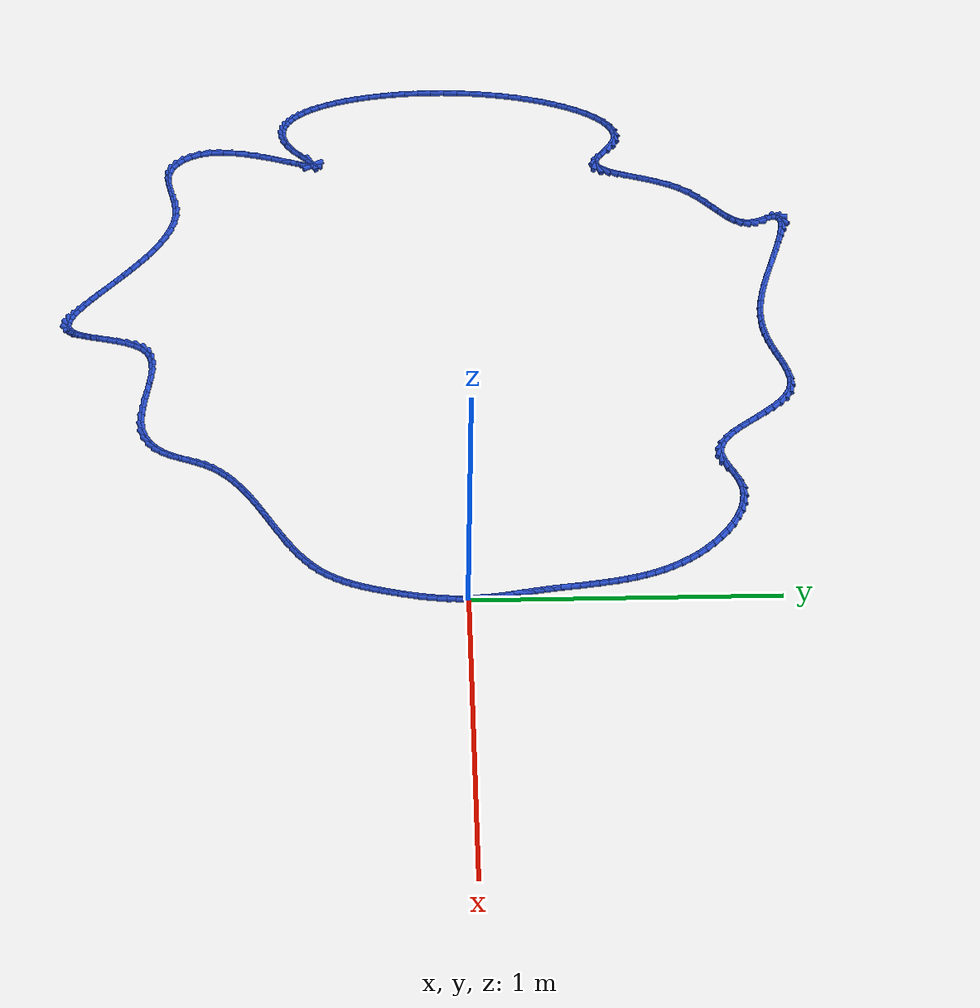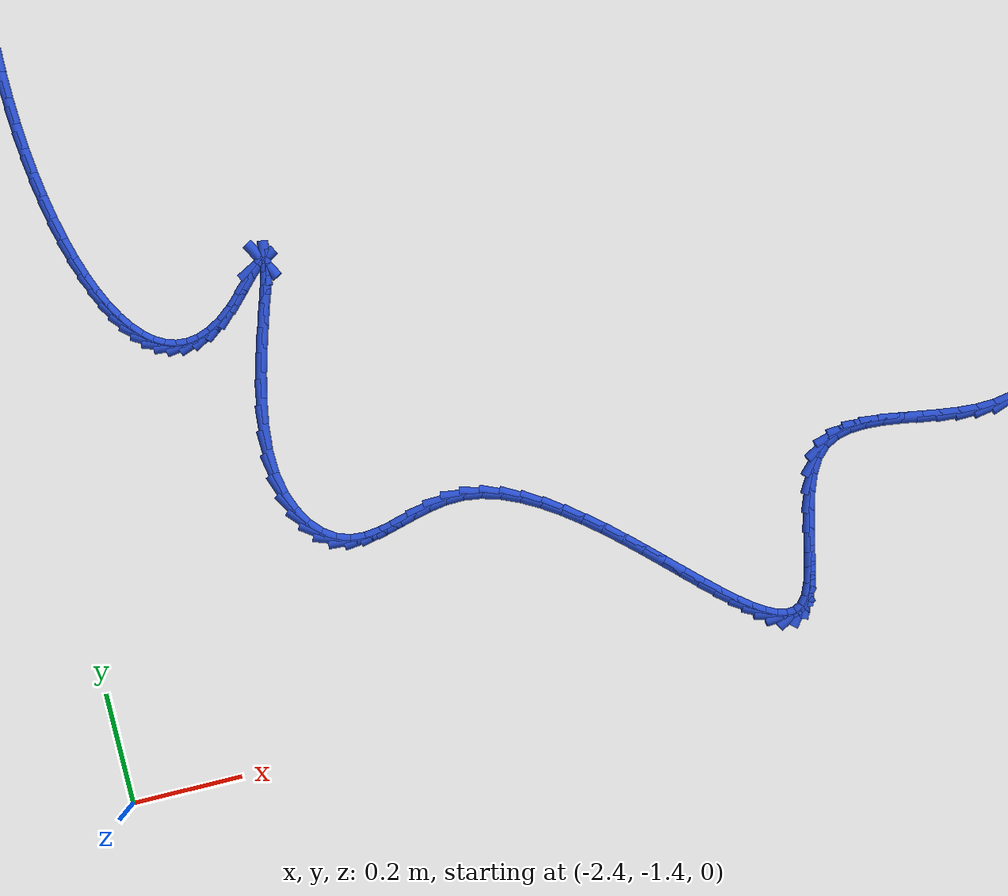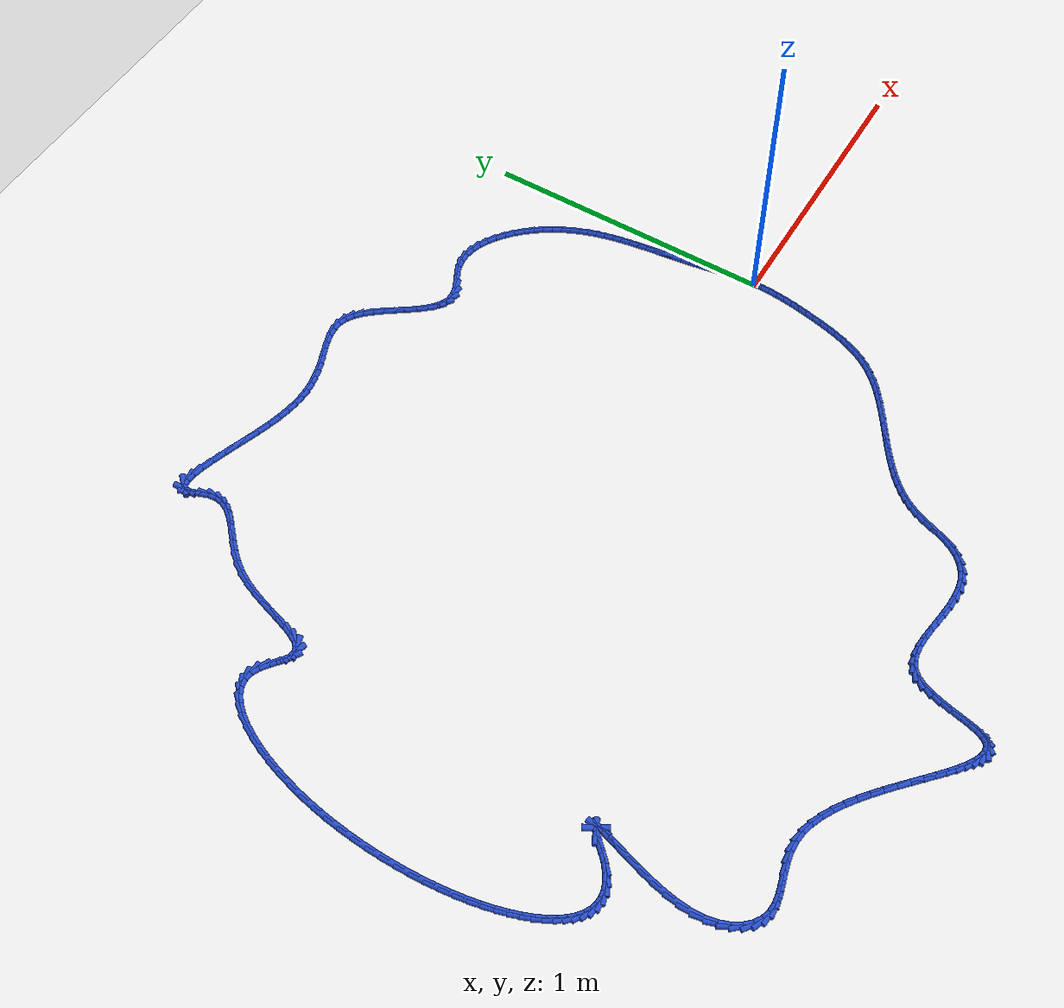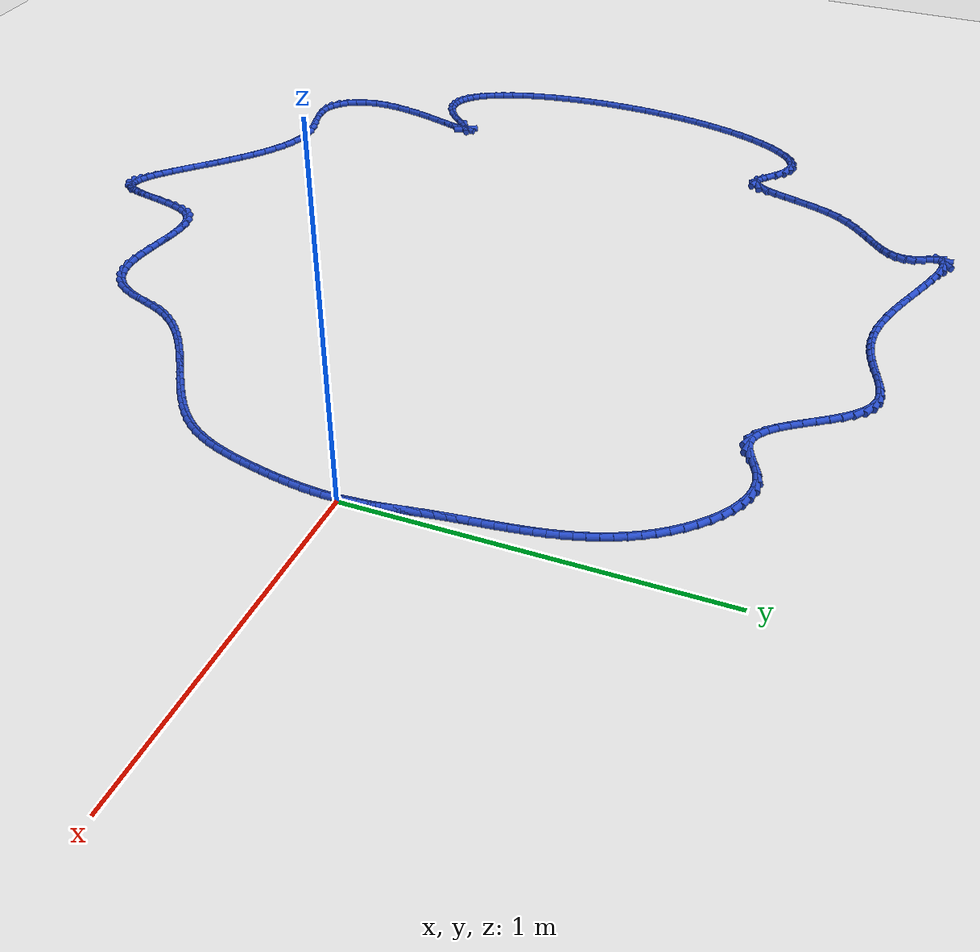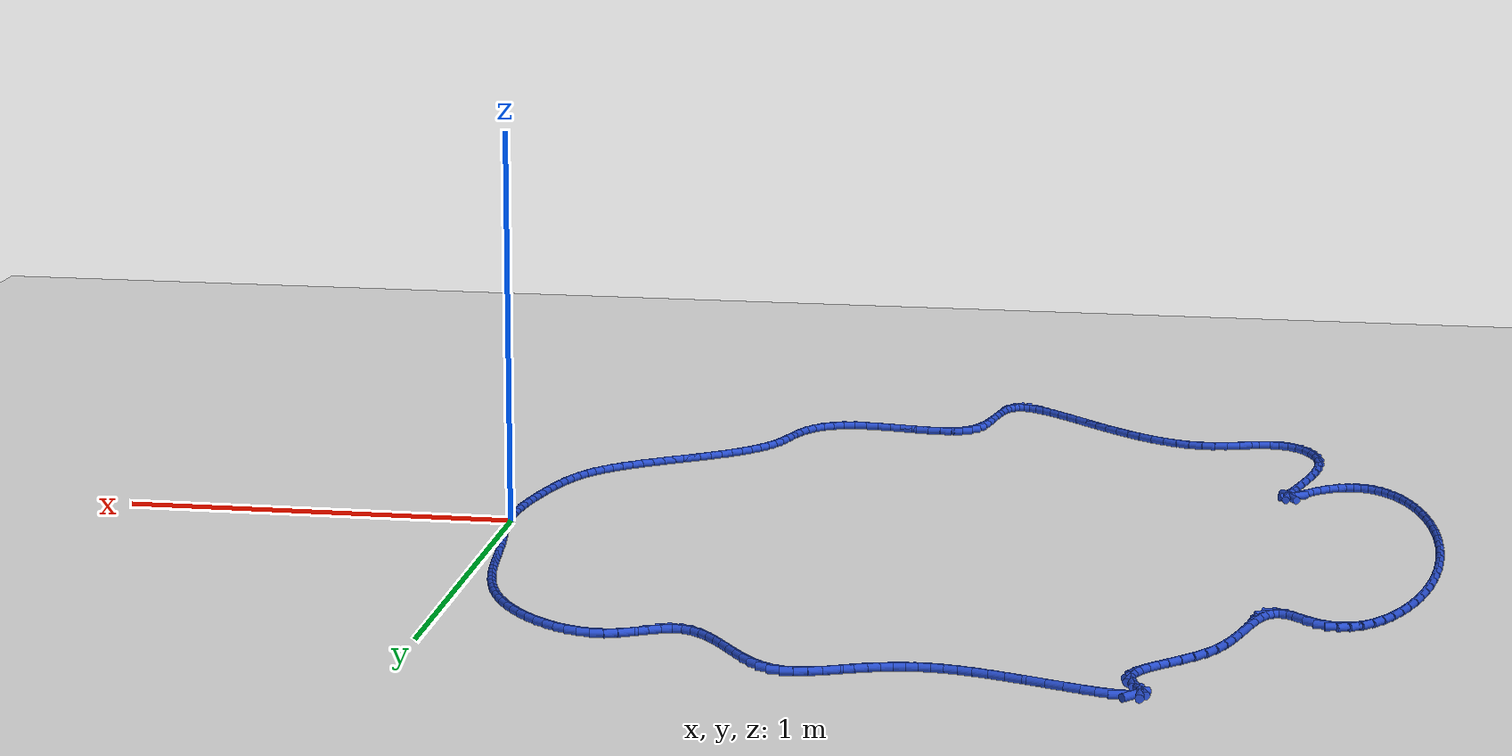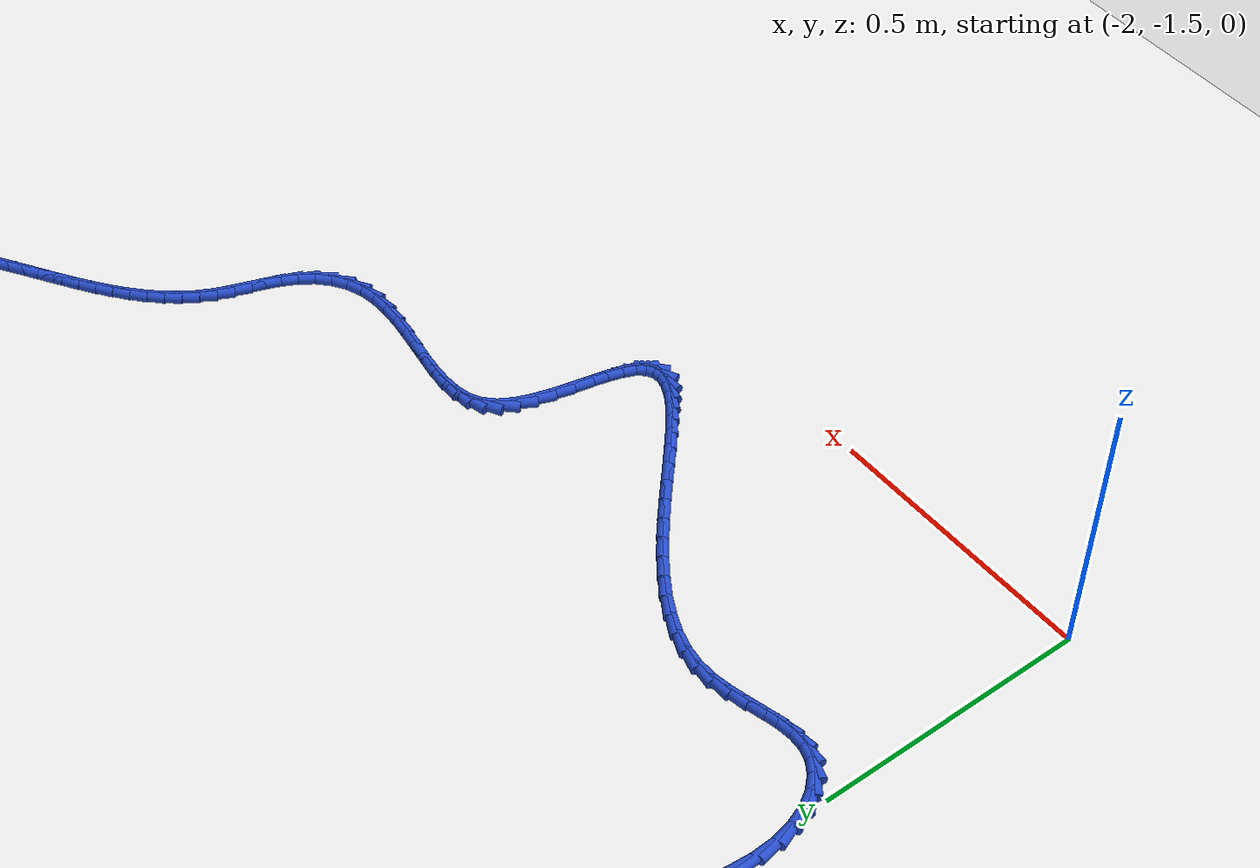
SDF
<sdf version="1.6">
 <world name="default">
  <light name="sun" type="directional">
   <pose>0 0 10 0 -0 0</pose>
   <diffuse>0.8 0.8 0.8 1</diffuse>
   <specular>0.2 0.2 0.2 1</specular>
   <attenuation>
    <range>1000</range>
    <constant>0.9</constant>
    <linear>0.01</linear>
    <quadratic>0.001</quadratic>
   </attenuation>
   <direction>-0.5 0.1 -0.9</direction>
  </light>
  <model name="ground_plane">
   <static>1</static>
   <link name="link">
    <collision name="collision">
     <geometry><plane><normal>0 0 1</normal><size>100 100</size></plane></geometry>
     <surface><friction><ode><mu>100</mu><mu2>50</mu2></ode></friction></surface>
    </collision>
    <visual name="visual">
     <cast_shadows>0</cast_shadows>
     <geometry><plane><normal>0 0 1</normal><size>100 100</size></plane></geometry>
     <material>
      <script><uri>file://media/materials/scripts/gazebo.material</uri><name>Gazebo/WhiteGlow</name></script>
     </material>
    </visual>
   </link>
  </model>
  <gravity>0 0 -9.8</gravity>
  <magnetic_field>6e-06 2.3e-05 -4.2e-05</magnetic_field>
  <atmosphere type="adiabatic"/>
  <physics name="default_physics" default="0" type="ode">
   <max_step_size>0.001</max_step_size>
   <real_time_factor>1</real_time_factor>
   <real_time_update_rate>1000</real_time_update_rate>
  </physics>
  <scene><ambient>0.4 0.4 0.4 1</ambient><background>0.7 0.7 0.7 1</background><shadows>1</shadows></scene>
  <spherical_coordinates>
   <surface_model>EARTH_WGS84</surface_model>
   <latitude_deg>0</latitude_deg>
   <longitude_deg>0</longitude_deg>
   <elevation>0</elevation>
   <heading_deg>0</heading_deg>
  </spherical_coordinates>
  <model name="line">
   <link name="link_0">
    <pose>-1.0408340855860843e-17 6.938893903907228e-18 0.01 0 1.57 -1.5288406629812028</pose>
    <collision name="collision">
     <geometry><cylinder><radius>0.01</radius><length>0.08</length></cylinder></geometry>
    </collision>
    <visual name="visual">
     <material>
      <script><name>Gazebo/Blue</name><uri>file://media/materials/scripts/gazebo.material</uri></script>
     </material>
     <geometry><cylinder><radius>0.01</radius><length>0.08</length></cylinder></geometry>
    </visual>
   </link>
   <link name="link_1">
    <pose>-0.0012697383187508027 0.030246052267149492 0.01 0 1.57 -1.4904389282044184</pose>
    <collision name="collision">
     <geometry><cylinder><radius>0.01</radius><length>0.08</length></cylinder></geometry>
    </collision>
    <visual name="visual">
     <material>
      <script><name>Gazebo/Blue</name><uri>file://media/materials/scripts/gazebo.material</uri></script>
     </material>
     <geometry><cylinder><radius>0.01</radius><length>0.08</length></cylinder></geometry>
    </visual>
   </link>
   <link name="link_2">
    <pose>-0.0037061450180958543 0.060500394377433826 0.01 0 1.57 -1.460066926359033</pose>
    <collision name="collision">
     <geometry><cylinder><radius>0.01</radius><length>0.08</length></cylinder></geometry>
    </collision>
    <visual name="visual">
     <material>
      <script><name>Gazebo/Blue</name><uri>file://media/materials/scripts/gazebo.material</uri></script>
     </material>
     <geometry><cylinder><radius>0.01</radius><length>0.08</length></cylinder></geometry>
    </visual>
   </link>
   <link name="link_3">
    <pose>-0.007071921407302899 0.09077247379385227 0.01 0 1.57 -1.4376629101199128</pose>
    <collision name="collision">
     <geometry><cylinder><radius>0.01</radius><length>0.08</length></cylinder></geometry>
    </collision>
    <visual name="visual">
     <material>
      <script><name>Gazebo/Blue</name><uri>file://media/materials/scripts/gazebo.material</uri></script>
     </material>
     <geometry><cylinder><radius>0.01</radius><length>0.08</length></cylinder></geometry>
    </visual>
   </link>
   <link name="link_4">
    <pose>-0.011129768795639691 0.12107173797940407 0.01 0 1.57 -1.423124094457603</pose>
    <collision name="collision">
     <geometry><cylinder><radius>0.01</radius><length>0.08</length></cylinder></geometry>
    </collision>
    <visual name="visual">
     <material>
      <script><name>Gazebo/Blue</name><uri>file://media/materials/scripts/gazebo.material</uri></script>
     </material>
     <geometry><cylinder><radius>0.01</radius><length>0.08</length></cylinder></geometry>
    </visual>
   </link>
   <link name="link_5">
    <pose>-0.015642388492373968 0.1514076343970886 0.01 0 1.57 -1.4163487453188346</pose>
    <collision name="collision">
     <geometry><cylinder><radius>0.01</radius><length>0.08</length></cylinder></geometry>
    </collision>
    <visual name="visual">
     <material>
      <script><name>Gazebo/Blue</name><uri>file://media/materials/scripts/gazebo.material</uri></script>
     </material>
     <geometry><cylinder><radius>0.01</radius><length>0.08</length></cylinder></geometry>
    </visual>
   </link>
   <link name="link_6">
    <pose>-0.020372481806773472 0.18178961050990505 0.01 0 1.57 -1.4172620975042012</pose>
    <collision name="collision">
     <geometry><cylinder><radius>0.01</radius><length>0.08</length></cylinder></geometry>
    </collision>
    <visual name="visual">
     <material>
      <script><name>Gazebo/Blue</name><uri>file://media/materials/scripts/gazebo.material</uri></script>
     </material>
     <geometry><cylinder><radius>0.01</radius><length>0.08</length></cylinder></geometry>
    </visual>
   </link>
   <link name="link_7">
    <pose>-0.025082750048105968 0.21222711378085282 0.01 0 1.57 -1.4258246507885837</pose>
    <collision name="collision">
     <geometry><cylinder><radius>0.01</radius><length>0.08</length></cylinder></geometry>
    </collision>
    <visual name="visual">
     <material>
      <script><name>Gazebo/Blue</name><uri>file://media/materials/scripts/gazebo.material</uri></script>
     </material>
     <geometry><cylinder><radius>0.01</radius><length>0.08</length></cylinder></geometry>
    </visual>
   </link>
   <link name="link_8">
    <pose>-0.02953598532157262 0.24272958178424622 0.01 0 1.57 -1.4391357886574705</pose>
    <collision name="collision">
     <geometry><cylinder><radius>0.01</radius><length>0.08</length></cylinder></geometry>
    </collision>
    <visual name="visual">
     <material>
      <script><name>Gazebo/Blue</name><uri>file://media/materials/scripts/gazebo.material</uri></script>
     </material>
     <geometry><cylinder><radius>0.01</radius><length>0.08</length></cylinder></geometry>
    </visual>
   </link>
   <link name="link_9">
    <pose>-0.033583894114097276 0.27329676833136585 0.01 0 1.57 -1.448885582735926</pose>
    <collision name="collision">
     <geometry><cylinder><radius>0.01</radius><length>0.08</length></cylinder></geometry>
    </collision>
    <visual name="visual">
     <material>
      <script><name>Gazebo/Blue</name><uri>file://media/materials/scripts/gazebo.material</uri></script>
     </material>
     <geometry><cylinder><radius>0.01</radius><length>0.08</length></cylinder></geometry>
    </visual>
   </link>
   <link name="link_10">
    <pose>-0.03733342735707603 0.3039006282805217 0.01 0 1.57 -1.4535992924206598</pose>
    <collision name="collision">
     <geometry><cylinder><radius>0.01</radius><length>0.08</length></cylinder></geometry>
    </collision>
    <visual name="visual">
     <material>
      <script><name>Gazebo/Blue</name><uri>file://media/materials/scripts/gazebo.material</uri></script>
     </material>
     <geometry><cylinder><radius>0.01</radius><length>0.08</length></cylinder></geometry>
    </visual>
   </link>
   <link name="link_11">
    <pose>-0.04093705310805319 0.3345081591697896 0.01 0 1.57 -1.4532762953830685</pose>
    <collision name="collision">
     <geometry><cylinder><radius>0.01</radius><length>0.08</length></cylinder></geometry>
    </collision>
    <visual name="visual">
     <material>
      <script><name>Gazebo/Blue</name><uri>file://media/materials/scripts/gazebo.material</uri></script>
     </material>
     <geometry><cylinder><radius>0.01</radius><length>0.08</length></cylinder></geometry>
    </visual>
   </link>
   <link name="link_12">
    <pose>-0.04454723942457301 0.36508635853724547 0.01 0 1.57 -1.447902208614132</pose>
    <collision name="collision">
     <geometry><cylinder><radius>0.01</radius><length>0.08</length></cylinder></geometry>
    </collision>
    <visual name="visual">
     <material>
      <script><name>Gazebo/Blue</name><uri>file://media/materials/scripts/gazebo.material</uri></script>
     </material>
     <geometry><cylinder><radius>0.01</radius><length>0.08</length></cylinder></geometry>
    </visual>
   </link>
   <link name="link_13">
    <pose>-0.048316454364179806 0.39560222392096533 0.01 0 1.57 -1.4374490125082795</pose>
    <collision name="collision">
     <geometry><cylinder><radius>0.01</radius><length>0.08</length></cylinder></geometry>
    </collision>
    <visual name="visual">
     <material>
      <script><name>Gazebo/Blue</name><uri>file://media/materials/scripts/gazebo.material</uri></script>
     </material>
     <geometry><cylinder><radius>0.01</radius><length>0.08</length></cylinder></geometry>
    </visual>
   </link>
   <link name="link_14">
    <pose>-0.052397165984417855 0.4260227528590252 0.01 0 1.57 -1.4218790060074933</pose>
    <collision name="collision">
     <geometry><cylinder><radius>0.01</radius><length>0.08</length></cylinder></geometry>
    </collision>
    <visual name="visual">
     <material>
      <script><name>Gazebo/Blue</name><uri>file://media/materials/scripts/gazebo.material</uri></script>
     </material>
     <geometry><cylinder><radius>0.01</radius><length>0.08</length></cylinder></geometry>
    </visual>
   </link>
   <link name="link_15">
    <pose>-0.05694184234283144 0.45631494288950075 0.01 0 1.57 -1.4011527974822453</pose>
    <collision name="collision">
     <geometry><cylinder><radius>0.01</radius><length>0.08</length></cylinder></geometry>
    </collision>
    <visual name="visual">
     <material>
      <script><name>Gazebo/Blue</name><uri>file://media/materials/scripts/gazebo.material</uri></script>
     </material>
     <geometry><cylinder><radius>0.01</radius><length>0.08</length></cylinder></geometry>
    </visual>
   </link>
   <link name="link_16">
    <pose>-0.06210295149696489 0.48644579155046824 0.01 0 1.57 -1.3752415856845936</pose>
    <collision name="collision">
     <geometry><cylinder><radius>0.01</radius><length>0.08</length></cylinder></geometry>
    </collision>
    <visual name="visual">
     <material>
      <script><name>Gazebo/Blue</name><uri>file://media/materials/scripts/gazebo.material</uri></script>
     </material>
     <geometry><cylinder><radius>0.01</radius><length>0.08</length></cylinder></geometry>
    </visual>
   </link>
   <link name="link_17">
    <pose>-0.06803296150436246 0.5163822963800035 0.01 0 1.57 -1.344143874009349</pose>
    <collision name="collision">
     <geometry><cylinder><radius>0.01</radius><length>0.08</length></cylinder></geometry>
    </collision>
    <visual name="visual">
     <material>
      <script><name>Gazebo/Blue</name><uri>file://media/materials/scripts/gazebo.material</uri></script>
     </material>
     <geometry><cylinder><radius>0.01</radius><length>0.08</length></cylinder></geometry>
    </visual>
   </link>
   <link name="link_18">
    <pose>-0.07488434042256846 0.5460914549161826 0.01 0 1.57 -1.307906394334803</pose>
    <collision name="collision">
     <geometry><cylinder><radius>0.01</radius><length>0.08</length></cylinder></geometry>
    </collision>
    <visual name="visual">
     <material>
      <script><name>Gazebo/Blue</name><uri>file://media/materials/scripts/gazebo.material</uri></script>
     </material>
     <geometry><cylinder><radius>0.01</radius><length>0.08</length></cylinder></geometry>
    </visual>
   </link>
   <link name="link_19">
    <pose>-0.08280955630912715 0.5755402646970813 0.01 0 1.57 -1.2666483099060637</pose>
    <collision name="collision">
     <geometry><cylinder><radius>0.01</radius><length>0.08</length></cylinder></geometry>
    </collision>
    <visual name="visual">
     <material>
      <script><name>Gazebo/Blue</name><uri>file://media/materials/scripts/gazebo.material</uri></script>
     </material>
     <geometry><cylinder><radius>0.01</radius><length>0.08</length></cylinder></geometry>
    </visual>
   </link>
   <link name="link_20">
    <pose>-0.09196107722158287 0.6046957232607757 0.01 0 1.57 -1.2205866968133137</pose>
    <collision name="collision">
     <geometry><cylinder><radius>0.01</radius><length>0.08</length></cylinder></geometry>
    </collision>
    <visual name="visual">
     <material>
      <script><name>Gazebo/Blue</name><uri>file://media/materials/scripts/gazebo.material</uri></script>
     </material>
     <geometry><cylinder><radius>0.01</radius><length>0.08</length></cylinder></geometry>
    </visual>
   </link>
   <link name="link_21">
    <pose>-0.10249137121747984 0.6335248281453415 0.01 0 1.57 -1.170059986261889</pose>
    <collision name="collision">
     <geometry><cylinder><radius>0.01</radius><length>0.08</length></cylinder></geometry>
    </collision>
    <visual name="visual">
     <material>
      <script><name>Gazebo/Blue</name><uri>file://media/materials/scripts/gazebo.material</uri></script>
     </material>
     <geometry><cylinder><radius>0.01</radius><length>0.08</length></cylinder></geometry>
    </visual>
   </link>
   <link name="link_22">
    <pose>-0.11455290635436238 0.6619945768888549 0.01 0 1.57 -1.1155448189650945</pose>
    <collision name="collision">
     <geometry><cylinder><radius>0.01</radius><length>0.08</length></cylinder></geometry>
    </collision>
    <visual name="visual">
     <material>
      <script><name>Gazebo/Blue</name><uri>file://media/materials/scripts/gazebo.material</uri></script>
     </material>
     <geometry><cylinder><radius>0.01</radius><length>0.08</length></cylinder></geometry>
    </visual>
   </link>
   <link name="link_23">
    <pose>-0.12829815068977485 0.6900719670293918 0.01 0 1.57 -1.057661183271682</pose>
    <collision name="collision">
     <geometry><cylinder><radius>0.01</radius><length>0.08</length></cylinder></geometry>
    </collision>
    <visual name="visual">
     <material>
      <script><name>Gazebo/Blue</name><uri>file://media/materials/scripts/gazebo.material</uri></script>
     </material>
     <geometry><cylinder><radius>0.01</radius><length>0.08</length></cylinder></geometry>
    </visual>
   </link>
   <link name="link_24">
    <pose>-0.14387957228126144 0.7177239961050281 0.01 0 1.57 -0.9971614300220978</pose>
    <collision name="collision">
     <geometry><cylinder><radius>0.01</radius><length>0.08</length></cylinder></geometry>
    </collision>
    <visual name="visual">
     <material>
      <script><name>Gazebo/Blue</name><uri>file://media/materials/scripts/gazebo.material</uri></script>
     </material>
     <geometry><cylinder><radius>0.01</radius><length>0.08</length></cylinder></geometry>
    </visual>
   </link>
   <link name="link_25">
    <pose>-0.16144963918636657 0.74491766165384 0.01 0 1.57 -0.934901107599358</pose>
    <collision name="collision">
     <geometry><cylinder><radius>0.01</radius><length>0.08</length></cylinder></geometry>
    </collision>
    <visual name="visual">
     <material>
      <script><name>Gazebo/Blue</name><uri>file://media/materials/scripts/gazebo.material</uri></script>
     </material>
     <geometry><cylinder><radius>0.01</radius><length>0.08</length></cylinder></geometry>
    </visual>
   </link>
   <link name="link_26">
    <pose>-0.18116053510137523 0.771619572263694 0.01 0 1.57 -0.8714266778772993</pose>
    <collision name="collision">
     <geometry><cylinder><radius>0.01</radius><length>0.08</length></cylinder></geometry>
    </collision>
    <visual name="visual">
     <material>
      <script><name>Gazebo/Blue</name><uri>file://media/materials/scripts/gazebo.material</uri></script>
     </material>
     <geometry><cylinder><radius>0.01</radius><length>0.08</length></cylinder></geometry>
    </visual>
   </link>
   <link name="link_27">
    <pose>-0.20305632550004468 0.7976484520836367 0.01 0 1.57 -0.8049261668410274</pose>
    <collision name="collision">
     <geometry><cylinder><radius>0.01</radius><length>0.08</length></cylinder></geometry>
    </collision>
    <visual name="visual">
     <material>
      <script><name>Gazebo/Blue</name><uri>file://media/materials/scripts/gazebo.material</uri></script>
     </material>
     <geometry><cylinder><radius>0.01</radius><length>0.08</length></cylinder></geometry>
    </visual>
   </link>
   <link name="link_28">
    <pose>-0.22691057141191293 0.8224530284481458 0.01 0 1.57 -0.7324234035653472</pose>
    <collision name="collision">
     <geometry><cylinder><radius>0.01</radius><length>0.08</length></cylinder></geometry>
    </collision>
    <visual name="visual">
     <material>
      <script><name>Gazebo/Blue</name><uri>file://media/materials/scripts/gazebo.material</uri></script>
     </material>
     <geometry><cylinder><radius>0.01</radius><length>0.08</length></cylinder></geometry>
    </visual>
   </link>
   <link name="link_29">
    <pose>-0.25245521777194213 0.8454251060689605 0.01 0 1.57 -0.6507271356398364</pose>
    <collision name="collision">
     <geometry><cylinder><radius>0.01</radius><length>0.08</length></cylinder></geometry>
    </collision>
    <visual name="visual">
     <material>
      <script><name>Gazebo/Blue</name><uri>file://media/materials/scripts/gazebo.material</uri></script>
     </material>
     <geometry><cylinder><radius>0.01</radius><length>0.08</length></cylinder></geometry>
    </visual>
   </link>
   <link name="link_30">
    <pose>-0.27942220951509394 0.8659564896578174 0.01 0 1.57 -0.5562097634579346</pose>
    <collision name="collision">
     <geometry><cylinder><radius>0.01</radius><length>0.08</length></cylinder></geometry>
    </collision>
    <visual name="visual">
     <material>
      <script><name>Gazebo/Blue</name><uri>file://media/materials/scripts/gazebo.material</uri></script>
     </material>
     <geometry><cylinder><radius>0.01</radius><length>0.08</length></cylinder></geometry>
    </visual>
   </link>
   <link name="link_31">
    <pose>-0.3075434915763307 0.8834389839264558 0.01 0 1.57 -0.44476497598986847</pose>
    <collision name="collision">
     <geometry><cylinder><radius>0.01</radius><length>0.08</length></cylinder></geometry>
    </collision>
    <visual name="visual">
     <material>
      <script><name>Gazebo/Blue</name><uri>file://media/materials/scripts/gazebo.material</uri></script>
     </material>
     <geometry><cylinder><radius>0.01</radius><length>0.08</length></cylinder></geometry>
    </visual>
   </link>
   <link name="link_32">
    <pose>-0.33655100889061407 0.8972643935866135 0.01 0 1.57 -0.312147691446262</pose>
    <collision name="collision">
     <geometry><cylinder><radius>0.01</radius><length>0.08</length></cylinder></geometry>
    </collision>
    <visual name="visual">
     <material>
      <script><name>Gazebo/Blue</name><uri>file://media/materials/scripts/gazebo.material</uri></script>
     </material>
     <geometry><cylinder><radius>0.01</radius><length>0.08</length></cylinder></geometry>
    </visual>
   </link>
   <link name="link_33">
    <pose>-0.3661767063929058 0.9068245233500281 0.01 0 1.57 -0.1550922311277548</pose>
    <collision name="collision">
     <geometry><cylinder><radius>0.01</radius><length>0.08</length></cylinder></geometry>
    </collision>
    <visual name="visual">
     <material>
      <script><name>Gazebo/Blue</name><uri>file://media/materials/scripts/gazebo.material</uri></script>
     </material>
     <geometry><cylinder><radius>0.01</radius><length>0.08</length></cylinder></geometry>
    </visual>
   </link>
   <link name="link_34">
    <pose>-0.39615252901816855 0.9115111779284383 0.01 0 1.57 0.02644332354930902</pose>
    <collision name="collision">
     <geometry><cylinder><radius>0.01</radius><length>0.08</length></cylinder></geometry>
    </collision>
    <visual name="visual">
     <material>
      <script><name>Gazebo/Blue</name><uri>file://media/materials/scripts/gazebo.material</uri></script>
     </material>
     <geometry><cylinder><radius>0.01</radius><length>0.08</length></cylinder></geometry>
    </visual>
   </link>
   <link name="link_35">
    <pose>-0.4262104217013638 0.910716162033582 0.01 0 1.57 0.22651418509251897</pose>
    <collision name="collision">
     <geometry><cylinder><radius>0.01</radius><length>0.08</length></cylinder></geometry>
    </collision>
    <visual name="visual">
     <material>
      <script><name>Gazebo/Blue</name><uri>file://media/materials/scripts/gazebo.material</uri></script>
     </material>
     <geometry><cylinder><radius>0.01</radius><length>0.08</length></cylinder></geometry>
    </visual>
   </link>
   <link name="link_36">
    <pose>-0.4560823281969345 0.9038316008324213 0.01 0 1.57 0.4054170350140008</pose>
    <collision name="collision">
     <geometry><cylinder><radius>0.01</radius><length>0.08</length></cylinder></geometry>
    </collision>
    <visual name="visual">
     <material>
      <script><name>Gazebo/Blue</name><uri>file://media/materials/scripts/gazebo.material</uri></script>
     </material>
     <geometry><cylinder><radius>0.01</radius><length>0.08</length></cylinder></geometry>
    </visual>
   </link>
   <link name="link_37">
    <pose>-0.48549666477637 0.8912071648956826 0.01 0 1.57 0.480564120621605</pose>
    <collision name="collision">
     <geometry><cylinder><radius>0.01</radius><length>0.08</length></cylinder></geometry>
    </collision>
    <visual name="visual">
     <material>
      <script><name>Gazebo/Blue</name><uri>file://media/materials/scripts/gazebo.material</uri></script>
     </material>
     <geometry><cylinder><radius>0.01</radius><length>0.08</length></cylinder></geometry>
    </visual>
   </link>
   <link name="link_38">
    <pose>-0.5141705524265512 0.8762586623208147 0.01 0 1.57 0.44673008761916644</pose>
    <collision name="collision">
     <geometry><cylinder><radius>0.01</radius><length>0.08</length></cylinder></geometry>
    </collision>
    <visual name="visual">
     <material>
      <script><name>Gazebo/Blue</name><uri>file://media/materials/scripts/gazebo.material</uri></script>
     </material>
     <geometry><cylinder><radius>0.01</radius><length>0.08</length></cylinder></geometry>
    </visual>
   </link>
   <link name="link_39">
    <pose>-0.5418188559932757 0.8630143371979422 0.01 0 1.57 0.27783956915048397</pose>
    <collision name="collision">
     <geometry><cylinder><radius>0.01</radius><length>0.08</length></cylinder></geometry>
    </collision>
    <visual name="visual">
     <material>
      <script><name>Gazebo/Blue</name><uri>file://media/materials/scripts/gazebo.material</uri></script>
     </material>
     <geometry><cylinder><radius>0.01</radius><length>0.08</length></cylinder></geometry>
    </visual>
   </link>
   <link name="link_40">
    <pose>-0.5681564419460365 0.8555024177707181 0.01 0 1.57 -0.05122189092899435</pose>
    <collision name="collision">
     <geometry><cylinder><radius>0.01</radius><length>0.08</length></cylinder></geometry>
    </collision>
    <visual name="visual">
     <material>
      <script><name>Gazebo/Blue</name><uri>file://media/materials/scripts/gazebo.material</uri></script>
     </material>
     <geometry><cylinder><radius>0.01</radius><length>0.08</length></cylinder></geometry>
    </visual>
   </link>
   <link name="link_41">
    <pose>-0.592998096170735 0.8567759682659938 0.01 0 1.57 -0.38386000757929223</pose>
    <collision name="collision">
     <geometry><cylinder><radius>0.01</radius><length>0.08</length></cylinder></geometry>
    </collision>
    <visual name="visual">
     <material>
      <script><name>Gazebo/Blue</name><uri>file://media/materials/scripts/gazebo.material</uri></script>
     </material>
     <geometry><cylinder><radius>0.01</radius><length>0.08</length></cylinder></geometry>
    </visual>
   </link>
   <link name="link_42">
    <pose>-0.616528329309562 0.8662797224036753 0.01 0 1.57 -0.6284700232140525</pose>
    <collision name="collision">
     <geometry><cylinder><radius>0.01</radius><length>0.08</length></cylinder></geometry>
    </collision>
    <visual name="visual">
     <material>
      <script><name>Gazebo/Blue</name><uri>file://media/materials/scripts/gazebo.material</uri></script>
     </material>
     <geometry><cylinder><radius>0.01</radius><length>0.08</length></cylinder></geometry>
    </visual>
   </link>
   <link name="link_43">
    <pose>-0.6390171483731505 0.882624011691677 0.01 0 1.57 -0.787184862463879</pose>
    <collision name="collision">
     <geometry><cylinder><radius>0.01</radius><length>0.08</length></cylinder></geometry>
    </collision>
    <visual name="visual">
     <material>
      <script><name>Gazebo/Blue</name><uri>file://media/materials/scripts/gazebo.material</uri></script>
     </material>
     <geometry><cylinder><radius>0.01</radius><length>0.08</length></cylinder></geometry>
    </visual>
   </link>
   <link name="link_44">
    <pose>-0.6607345603721327 0.9044191676379122 0.01 0 1.57 -0.883659591239229</pose>
    <collision name="collision">
     <geometry><cylinder><radius>0.01</radius><length>0.08</length></cylinder></geometry>
    </collision>
    <visual name="visual">
     <material>
      <script><name>Gazebo/Blue</name><uri>file://media/materials/scripts/gazebo.material</uri></script>
     </material>
     <geometry><cylinder><radius>0.01</radius><length>0.08</length></cylinder></geometry>
    </visual>
   </link>
   <link name="link_45">
    <pose>-0.6819505723171412 0.9302755217502945 0.01 0 1.57 -0.936586296262233</pose>
    <collision name="collision">
     <geometry><cylinder><radius>0.01</radius><length>0.08</length></cylinder></geometry>
    </collision>
    <visual name="visual">
     <material>
      <script><name>Gazebo/Blue</name><uri>file://media/materials/scripts/gazebo.material</uri></script>
     </material>
     <geometry><cylinder><radius>0.01</radius><length>0.08</length></cylinder></geometry>
    </visual>
   </link>
   <link name="link_46">
    <pose>-0.7029351912188082 0.9588034055367384 0.01 0 1.57 -0.9565575671919775</pose>
    <collision name="collision">
     <geometry><cylinder><radius>0.01</radius><length>0.08</length></cylinder></geometry>
    </collision>
    <visual name="visual">
     <material>
      <script><name>Gazebo/Blue</name><uri>file://media/materials/scripts/gazebo.material</uri></script>
     </material>
     <geometry><cylinder><radius>0.01</radius><length>0.08</length></cylinder></geometry>
    </visual>
   </link>
   <link name="link_47">
    <pose>-0.7239584240877663 0.9886131505051574 0.01 0 1.57 -0.9479614718937222</pose>
    <collision name="collision">
     <geometry><cylinder><radius>0.01</radius><length>0.08</length></cylinder></geometry>
    </collision>
    <visual name="visual">
     <material>
      <script><name>Gazebo/Blue</name><uri>file://media/materials/scripts/gazebo.material</uri></script>
     </material>
     <geometry><cylinder><radius>0.01</radius><length>0.08</length></cylinder></geometry>
    </visual>
   </link>
   <link name="link_48">
    <pose>-0.745290277934648 1.018315088163465 0.01 0 1.57 -0.9103349078859827</pose>
    <collision name="collision">
     <geometry><cylinder><radius>0.01</radius><length>0.08</length></cylinder></geometry>
    </collision>
    <visual name="visual">
     <material>
      <script><name>Gazebo/Blue</name><uri>file://media/materials/scripts/gazebo.material</uri></script>
     </material>
     <geometry><cylinder><radius>0.01</radius><length>0.08</length></cylinder></geometry>
    </visual>
   </link>
   <link name="link_49">
    <pose>-0.7672007597700857 1.0465195500195752 0.01 0 1.57 -0.8385591434796962</pose>
    <collision name="collision">
     <geometry><cylinder><radius>0.01</radius><length>0.08</length></cylinder></geometry>
    </collision>
    <visual name="visual">
     <material>
      <script><name>Gazebo/Blue</name><uri>file://media/materials/scripts/gazebo.material</uri></script>
     </material>
     <geometry><cylinder><radius>0.01</radius><length>0.08</length></cylinder></geometry>
    </visual>
   </link>
   <link name="link_50">
    <pose>-0.789959876604712 1.0718368675814023 0.01 0 1.57 -0.7223171470292652</pose>
    <collision name="collision">
     <geometry><cylinder><radius>0.01</radius><length>0.08</length></cylinder></geometry>
    </collision>
    <visual name="visual">
     <material>
      <script><name>Gazebo/Blue</name><uri>file://media/materials/scripts/gazebo.material</uri></script>
     </material>
     <geometry><cylinder><radius>0.01</radius><length>0.08</length></cylinder></geometry>
    </visual>
   </link>
   <link name="link_51">
    <pose>-0.8138376354491592 1.0928773723568592 0.01 0 1.57 -0.54662915295404</pose>
    <collision name="collision">
     <geometry><cylinder><radius>0.01</radius><length>0.08</length></cylinder></geometry>
    </collision>
    <visual name="visual">
     <material>
      <script><name>Gazebo/Blue</name><uri>file://media/materials/scripts/gazebo.material</uri></script>
     </material>
     <geometry><cylinder><radius>0.01</radius><length>0.08</length></cylinder></geometry>
    </visual>
   </link>
   <link name="link_52">
    <pose>-0.8391040433140595 1.1082513958538602 0.01 0 1.57 -0.29992006252335646</pose>
    <collision name="collision">
     <geometry><cylinder><radius>0.01</radius><length>0.08</length></cylinder></geometry>
    </collision>
    <visual name="visual">
     <material>
      <script><name>Gazebo/Blue</name><uri>file://media/materials/scripts/gazebo.material</uri></script>
     </material>
     <geometry><cylinder><radius>0.01</radius><length>0.08</length></cylinder></geometry>
    </visual>
   </link>
   <link name="link_53">
    <pose>-0.8660270476735114 1.1165772990143359 0.01 0 1.57 -0.03115331940229374</pose>
    <collision name="collision">
     <geometry><cylinder><radius>0.01</radius><length>0.08</length></cylinder></geometry>
    </collision>
    <visual name="visual">
     <material>
      <script><name>Gazebo/Blue</name><uri>file://media/materials/scripts/gazebo.material</uri></script>
     </material>
     <geometry><cylinder><radius>0.01</radius><length>0.08</length></cylinder></geometry>
    </visual>
   </link>
   <link name="link_54">
    <pose>-0.8946194079927946 1.1174683342250766 0.01 0 1.57 0.16590258207798814</pose>
    <collision name="collision">
     <geometry><cylinder><radius>0.01</radius><length>0.08</length></cylinder></geometry>
    </collision>
    <visual name="visual">
     <material>
      <script><name>Gazebo/Blue</name><uri>file://media/materials/scripts/gazebo.material</uri></script>
     </material>
     <geometry><cylinder><radius>0.01</radius><length>0.08</length></cylinder></geometry>
    </visual>
   </link>
   <link name="link_55">
    <pose>-0.9243950190607217 1.112482657949913 0.01 0 1.57 0.2900837668800088</pose>
    <collision name="collision">
     <geometry><cylinder><radius>0.01</radius><length>0.08</length></cylinder></geometry>
    </collision>
    <visual name="visual">
     <material>
      <script><name>Gazebo/Blue</name><uri>file://media/materials/scripts/gazebo.material</uri></script>
     </material>
     <geometry><cylinder><radius>0.01</radius><length>0.08</length></cylinder></geometry>
    </visual>
   </link>
   <link name="link_56">
    <pose>-0.9548100028749165 1.1034036631595348 0.01 0 1.57 0.35726097831734493</pose>
    <collision name="collision">
     <geometry><cylinder><radius>0.01</radius><length>0.08</length></cylinder></geometry>
    </collision>
    <visual name="visual">
     <material>
      <script><name>Gazebo/Blue</name><uri>file://media/materials/scripts/gazebo.material</uri></script>
     </material>
     <geometry><cylinder><radius>0.01</radius><length>0.08</length></cylinder></geometry>
    </visual>
   </link>
   <link name="link_57">
    <pose>-0.9853204814330031 1.0920147428246325 0.01 0 1.57 0.37736568619807154</pose>
    <collision name="collision">
     <geometry><cylinder><radius>0.01</radius><length>0.08</length></cylinder></geometry>
    </collision>
    <visual name="visual">
     <material>
      <script><name>Gazebo/Blue</name><uri>file://media/materials/scripts/gazebo.material</uri></script>
     </material>
     <geometry><cylinder><radius>0.01</radius><length>0.08</length></cylinder></geometry>
    </visual>
   </link>
   <link name="link_58">
    <pose>-1.0153825767326066 1.0800992899158959 0.01 0 1.57 0.3526654235209021</pose>
    <collision name="collision">
     <geometry><cylinder><radius>0.01</radius><length>0.08</length></cylinder></geometry>
    </collision>
    <visual name="visual">
     <material>
      <script><name>Gazebo/Blue</name><uri>file://media/materials/scripts/gazebo.material</uri></script>
     </material>
     <geometry><cylinder><radius>0.01</radius><length>0.08</length></cylinder></geometry>
    </visual>
   </link>
   <link name="link_59">
    <pose>-1.0444818400322136 1.0693892471683886 0.01 0 1.57 0.29883495750355027</pose>
    <collision name="collision">
     <geometry><cylinder><radius>0.01</radius><length>0.08</length></cylinder></geometry>
    </collision>
    <visual name="visual">
     <material>
      <script><name>Gazebo/Blue</name><uri>file://media/materials/scripts/gazebo.material</uri></script>
     </material>
     <geometry><cylinder><radius>0.01</radius><length>0.08</length></cylinder></geometry>
    </visual>
   </link>
   <link name="link_60">
    <pose>-1.0726152371105215 1.060722467666409 0.01 0 1.57 0.23280434635918168</pose>
    <collision name="collision">
     <geometry><cylinder><radius>0.01</radius><length>0.08</length></cylinder></geometry>
    </collision>
    <visual name="visual">
     <material>
      <script><name>Gazebo/Blue</name><uri>file://media/materials/scripts/gazebo.material</uri></script>
     </material>
     <geometry><cylinder><radius>0.01</radius><length>0.08</length></cylinder></geometry>
    </visual>
   </link>
   <link name="link_61">
    <pose>-1.1002132612494266 1.0541788822245142 0.01 0 1.57 0.1573557138279378</pose>
    <collision name="collision">
     <geometry><cylinder><radius>0.01</radius><length>0.08</length></cylinder></geometry>
    </collision>
    <visual name="visual">
     <material>
      <script><name>Gazebo/Blue</name><uri>file://media/materials/scripts/gazebo.material</uri></script>
     </material>
     <geometry><cylinder><radius>0.01</radius><length>0.08</length></cylinder></geometry>
    </visual>
   </link>
   <link name="link_62">
    <pose>-1.1277201241595456 1.0498144381670482 0.01 0 1.57 0.07628248743457965</pose>
    <collision name="collision">
     <geometry><cylinder><radius>0.01</radius><length>0.08</length></cylinder></geometry>
    </collision>
    <visual name="visual">
     <material>
      <script><name>Gazebo/Blue</name><uri>file://media/materials/scripts/gazebo.material</uri></script>
     </material>
     <geometry><cylinder><radius>0.01</radius><length>0.08</length></cylinder></geometry>
    </visual>
   </link>
   <link name="link_63">
    <pose>-1.1555800375514933 1.0476850828183537 0.01 0 1.57 -0.005641831955613951</pose>
    <collision name="collision">
     <geometry><cylinder><radius>0.01</radius><length>0.08</length></cylinder></geometry>
    </collision>
    <visual name="visual">
     <material>
      <script><name>Gazebo/Blue</name><uri>file://media/materials/scripts/gazebo.material</uri></script>
     </material>
     <geometry><cylinder><radius>0.01</radius><length>0.08</length></cylinder></geometry>
    </visual>
   </link>
   <link name="link_64">
    <pose>-1.184237213135885 1.0478467635027735 0.01 0 1.57 -0.08370952217097634</pose>
    <collision name="collision">
     <geometry><cylinder><radius>0.01</radius><length>0.08</length></cylinder></geometry>
    </collision>
    <visual name="visual">
     <material>
      <script><name>Gazebo/Blue</name><uri>file://media/materials/scripts/gazebo.material</uri></script>
     </material>
     <geometry><cylinder><radius>0.01</radius><length>0.08</length></cylinder></geometry>
    </visual>
   </link>
   <link name="link_65">
    <pose>-1.2141358626233358 1.0503554275446507 0.01 0 1.57 -0.1542716616432093</pose>
    <collision name="collision">
     <geometry><cylinder><radius>0.01</radius><length>0.08</length></cylinder></geometry>
    </collision>
    <visual name="visual">
     <material>
      <script><name>Gazebo/Blue</name><uri>file://media/materials/scripts/gazebo.material</uri></script>
     </material>
     <geometry><cylinder><radius>0.01</radius><length>0.08</length></cylinder></geometry>
    </visual>
   </link>
   <link name="link_66">
    <pose>-1.2457201977244614 1.0552670222683287 0.01 0 1.57 -0.2152298746873299</pose>
    <collision name="collision">
     <geometry><cylinder><radius>0.01</radius><length>0.08</length></cylinder></geometry>
    </collision>
    <visual name="visual">
     <material>
      <script><name>Gazebo/Blue</name><uri>file://media/materials/scripts/gazebo.material</uri></script>
     </material>
     <geometry><cylinder><radius>0.01</radius><length>0.08</length></cylinder></geometry>
    </visual>
   </link>
   <link name="link_67">
    <pose>-1.279434430149878 1.062637494998151 0.01 0 1.57 -0.26595648585456066</pose>
    <collision name="collision">
     <geometry><cylinder><radius>0.01</radius><length>0.08</length></cylinder></geometry>
    </collision>
    <visual name="visual">
     <material>
      <script><name>Gazebo/Blue</name><uri>file://media/materials/scripts/gazebo.material</uri></script>
     </material>
     <geometry><cylinder><radius>0.01</radius><length>0.08</length></cylinder></geometry>
    </visual>
   </link>
   <link name="link_68">
    <pose>-1.3157227716101991 1.0725227930584595 0.01 0 1.57 -0.3067148833372153</pose>
    <collision name="collision">
     <geometry><cylinder><radius>0.01</radius><length>0.08</length></cylinder></geometry>
    </collision>
    <visual name="visual">
     <material>
      <script><name>Gazebo/Blue</name><uri>file://media/materials/scripts/gazebo.material</uri></script>
     </material>
     <geometry><cylinder><radius>0.01</radius><length>0.08</length></cylinder></geometry>
    </visual>
   </link>
   <link name="link_69">
    <pose>-1.3550069654204289 1.0849644546546386 0.01 0 1.57 -0.3336329036697023</pose>
    <collision name="collision">
     <geometry><cylinder><radius>0.01</radius><length>0.08</length></cylinder></geometry>
    </collision>
    <visual name="visual">
     <material>
      <script><name>Gazebo/Blue</name><uri>file://media/materials/scripts/gazebo.material</uri></script>
     </material>
     <geometry><cylinder><radius>0.01</radius><length>0.08</length></cylinder></geometry>
    </visual>
   </link>
   <link name="link_70">
    <pose>-1.3968958062239416 1.0994826690573574 0.01 0 1.57 -0.3445390470672556</pose>
    <collision name="collision">
     <geometry><cylinder><radius>0.01</radius><length>0.08</length></cylinder></geometry>
    </collision>
    <visual name="visual">
     <material>
      <script><name>Gazebo/Blue</name><uri>file://media/materials/scripts/gazebo.material</uri></script>
     </material>
     <geometry><cylinder><radius>0.01</radius><length>0.08</length></cylinder></geometry>
    </visual>
   </link>
   <link name="link_71">
    <pose>-1.4399757701598996 1.1149420064536801 0.01 0 1.57 -0.34178565242473385</pose>
    <collision name="collision">
     <geometry><cylinder><radius>0.01</radius><length>0.08</length></cylinder></geometry>
    </collision>
    <visual name="visual">
     <material>
      <script><name>Gazebo/Blue</name><uri>file://media/materials/scripts/gazebo.material</uri></script>
     </material>
     <geometry><cylinder><radius>0.01</radius><length>0.08</length></cylinder></geometry>
    </visual>
   </link>
   <link name="link_72">
    <pose>-1.4827683004644931 1.1301653310338857 0.01 0 1.57 -0.3247017369798717</pose>
    <collision name="collision">
     <geometry><cylinder><radius>0.01</radius><length>0.08</length></cylinder></geometry>
    </collision>
    <visual name="visual">
     <material>
      <script><name>Gazebo/Blue</name><uri>file://media/materials/scripts/gazebo.material</uri></script>
     </material>
     <geometry><cylinder><radius>0.01</radius><length>0.08</length></cylinder></geometry>
    </visual>
   </link>
   <link name="link_73">
    <pose>-1.523794840373912 1.143975506988253 0.01 0 1.57 -0.2886691469584685</pose>
    <collision name="collision">
     <geometry><cylinder><radius>0.01</radius><length>0.08</length></cylinder></geometry>
    </collision>
    <visual name="visual">
     <material>
      <script><name>Gazebo/Blue</name><uri>file://media/materials/scripts/gazebo.material</uri></script>
     </material>
     <geometry><cylinder><radius>0.01</radius><length>0.08</length></cylinder></geometry>
    </visual>
   </link>
   <link name="link_74">
    <pose>-1.5615768331243458 1.1551953985070593 0.01 0 1.57 -0.2217238565416612</pose>
    <collision name="collision">
     <geometry><cylinder><radius>0.01</radius><length>0.08</length></cylinder></geometry>
    </collision>
    <visual name="visual">
     <material>
      <script><name>Gazebo/Blue</name><uri>file://media/materials/scripts/gazebo.material</uri></script>
     </material>
     <geometry><cylinder><radius>0.01</radius><length>0.08</length></cylinder></geometry>
    </visual>
   </link>
   <link name="link_75">
    <pose>-1.5946357219519847 1.162647869780584 0.01 0 1.57 -0.09310952172858304</pose>
    <collision name="collision">
     <geometry><cylinder><radius>0.01</radius><length>0.08</length></cylinder></geometry>
    </collision>
    <visual name="visual">
     <material>
      <script><name>Gazebo/Blue</name><uri>file://media/materials/scripts/gazebo.material</uri></script>
     </material>
     <geometry><cylinder><radius>0.01</radius><length>0.08</length></cylinder></geometry>
    </visual>
   </link>
   <link name="link_76">
    <pose>-1.6214929500930175 1.1651557849991054 0.01 0 1.57 0.18625892993723173</pose>
    <collision name="collision">
     <geometry><cylinder><radius>0.01</radius><length>0.08</length></cylinder></geometry>
    </collision>
    <visual name="visual">
     <material>
      <script><name>Gazebo/Blue</name><uri>file://media/materials/scripts/gazebo.material</uri></script>
     </material>
     <geometry><cylinder><radius>0.01</radius><length>0.08</length></cylinder></geometry>
    </visual>
   </link>
   <link name="link_77">
    <pose>-1.640669960783634 1.1615420083529016 0.01 0 1.57 0.8281018526046393</pose>
    <collision name="collision">
     <geometry><cylinder><radius>0.01</radius><length>0.08</length></cylinder></geometry>
    </collision>
    <visual name="visual">
     <material>
      <script><name>Gazebo/Blue</name><uri>file://media/materials/scripts/gazebo.material</uri></script>
     </material>
     <geometry><cylinder><radius>0.01</radius><length>0.08</length></cylinder></geometry>
    </visual>
   </link>
   <link name="link_78">
    <pose>-1.6506881972600245 1.1506294040322507 0.01 0 1.57 -1.5388955093673296</pose>
    <collision name="collision">
     <geometry><cylinder><radius>0.01</radius><length>0.08</length></cylinder></geometry>
    </collision>
    <visual name="visual">
     <material>
      <script><name>Gazebo/Blue</name><uri>file://media/materials/scripts/gazebo.material</uri></script>
     </material>
     <geometry><cylinder><radius>0.01</radius><length>0.08</length></cylinder></geometry>
    </visual>
   </link>
   <link name="link_79">
    <pose>-1.650069483856134 1.1312410761108918 0.01 0 1.57 -1.2121774962967475</pose>
    <collision name="collision">
     <geometry><cylinder><radius>0.01</radius><length>0.08</length></cylinder></geometry>
    </collision>
    <visual name="visual">
     <material>
      <script><name>Gazebo/Blue</name><uri>file://media/materials/scripts/gazebo.material</uri></script>
     </material>
     <geometry><cylinder><radius>0.01</radius><length>0.08</length></cylinder></geometry>
    </visual>
   </link>
   <link name="link_80">
    <pose>-1.6397549625357062 1.1037229775235444 0.01 0 1.57 -1.2237248663936668</pose>
    <collision name="collision">
     <geometry><cylinder><radius>0.01</radius><length>0.08</length></cylinder></geometry>
    </collision>
    <visual name="visual">
     <material>
      <script><name>Gazebo/Blue</name><uri>file://media/materials/scripts/gazebo.material</uri></script>
     </material>
     <geometry><cylinder><radius>0.01</radius><length>0.08</length></cylinder></geometry>
    </visual>
   </link>
   <link name="link_81">
    <pose>-1.6288430753548777 1.0735557485010208 0.01 0 1.57 -1.4518259964928009</pose>
    <collision name="collision">
     <geometry><cylinder><radius>0.01</radius><length>0.08</length></cylinder></geometry>
    </collision>
    <visual name="visual">
     <material>
      <script><name>Gazebo/Blue</name><uri>file://media/materials/scripts/gazebo.material</uri></script>
     </material>
     <geometry><cylinder><radius>0.01</radius><length>0.08</length></cylinder></geometry>
    </visual>
   </link>
   <link name="link_82">
    <pose>-1.6255141956434513 1.0457071304805285 0.01 0 1.57 1.3953311796545813</pose>
    <collision name="collision">
     <geometry><cylinder><radius>0.01</radius><length>0.08</length></cylinder></geometry>
    </collision>
    <visual name="visual">
     <material>
      <script><name>Gazebo/Blue</name><uri>file://media/materials/scripts/gazebo.material</uri></script>
     </material>
     <geometry><cylinder><radius>0.01</radius><length>0.08</length></cylinder></geometry>
    </visual>
   </link>
   <link name="link_83">
    <pose>-1.6300107861077717 1.0203439828467478 0.01 0 1.57 1.1321482320393972</pose>
    <collision name="collision">
     <geometry><cylinder><radius>0.01</radius><length>0.08</length></cylinder></geometry>
    </collision>
    <visual name="visual">
     <material>
      <script><name>Gazebo/Blue</name><uri>file://media/materials/scripts/gazebo.material</uri></script>
     </material>
     <geometry><cylinder><radius>0.01</radius><length>0.08</length></cylinder></geometry>
    </visual>
   </link>
   <link name="link_84">
    <pose>-1.6410873067999305 0.9967332146604292 0.01 0 1.57 0.9425577557538525</pose>
    <collision name="collision">
     <geometry><cylinder><radius>0.01</radius><length>0.08</length></cylinder></geometry>
    </collision>
    <visual name="visual">
     <material>
      <script><name>Gazebo/Blue</name><uri>file://media/materials/scripts/gazebo.material</uri></script>
     </material>
     <geometry><cylinder><radius>0.01</radius><length>0.08</length></cylinder></geometry>
    </visual>
   </link>
   <link name="link_85">
    <pose>-1.6574982177720226 0.9741417349823239 0.01 0 1.57 0.827553270187208</pose>
    <collision name="collision">
     <geometry><cylinder><radius>0.01</radius><length>0.08</length></cylinder></geometry>
    </collision>
    <visual name="visual">
     <material>
      <script><name>Gazebo/Blue</name><uri>file://media/materials/scripts/gazebo.material</uri></script>
     </material>
     <geometry><cylinder><radius>0.01</radius><length>0.08</length></cylinder></geometry>
    </visual>
   </link>
   <link name="link_86">
    <pose>-1.6779979790761412 0.9518364528731819 0.01 0 1.57 0.7725798387005676</pose>
    <collision name="collision">
     <geometry><cylinder><radius>0.01</radius><length>0.08</length></cylinder></geometry>
    </collision>
    <visual name="visual">
     <material>
      <script><name>Gazebo/Blue</name><uri>file://media/materials/scripts/gazebo.material</uri></script>
     </material>
     <geometry><cylinder><radius>0.01</radius><length>0.08</length></cylinder></geometry>
    </visual>
   </link>
   <link name="link_87">
    <pose>-1.7013410507643785 0.9290842773937539 0.01 0 1.57 0.7647622476055279</pose>
    <collision name="collision">
     <geometry><cylinder><radius>0.01</radius><length>0.08</length></cylinder></geometry>
    </collision>
    <visual name="visual">
     <material>
      <script><name>Gazebo/Blue</name><uri>file://media/materials/scripts/gazebo.material</uri></script>
     </material>
     <geometry><cylinder><radius>0.01</radius><length>0.08</length></cylinder></geometry>
    </visual>
   </link>
   <link name="link_88">
    <pose>-1.7262818928888286 0.9051521176047906 0.01 0 1.57 0.7961951763216546</pose>
    <collision name="collision">
     <geometry><cylinder><radius>0.01</radius><length>0.08</length></cylinder></geometry>
    </collision>
    <visual name="visual">
     <material>
      <script><name>Gazebo/Blue</name><uri>file://media/materials/scripts/gazebo.material</uri></script>
     </material>
     <geometry><cylinder><radius>0.01</radius><length>0.08</length></cylinder></geometry>
    </visual>
   </link>
   <link name="link_89">
    <pose>-1.751574965501584 0.8793068825670426 0.01 0 1.57 0.8626039720072615</pose>
    <collision name="collision">
     <geometry><cylinder><radius>0.01</radius><length>0.08</length></cylinder></geometry>
    </collision>
    <visual name="visual">
     <material>
      <script><name>Gazebo/Blue</name><uri>file://media/materials/scripts/gazebo.material</uri></script>
     </material>
     <geometry><cylinder><radius>0.01</radius><length>0.08</length></cylinder></geometry>
    </visual>
   </link>
   <link name="link_90">
    <pose>-1.7759747286547394 0.8508154813412606 0.01 0 1.57 0.9610934121542455</pose>
    <collision name="collision">
     <geometry><cylinder><radius>0.01</radius><length>0.08</length></cylinder></geometry>
    </collision>
    <visual name="visual">
     <material>
      <script><name>Gazebo/Blue</name><uri>file://media/materials/scripts/gazebo.material</uri></script>
     </material>
     <geometry><cylinder><radius>0.01</radius><length>0.08</length></cylinder></geometry>
    </visual>
   </link>
   <link name="link_91">
    <pose>-1.7982356424003871 0.8189448229881945 0.01 0 1.57 1.0790997635239163</pose>
    <collision name="collision">
     <geometry><cylinder><radius>0.01</radius><length>0.08</length></cylinder></geometry>
    </collision>
    <visual name="visual">
     <material>
      <script><name>Gazebo/Blue</name><uri>file://media/materials/scripts/gazebo.material</uri></script>
     </material>
     <geometry><cylinder><radius>0.01</radius><length>0.08</length></cylinder></geometry>
    </visual>
   </link>
   <link name="link_92">
    <pose>-1.8173534338852138 0.7832486222638266 0.01 0 1.57 1.1717818792761356</pose>
    <collision name="collision">
     <geometry><cylinder><radius>0.01</radius><length>0.08</length></cylinder></geometry>
    </collision>
    <visual name="visual">
     <material>
      <script><name>Gazebo/Blue</name><uri>file://media/materials/scripts/gazebo.material</uri></script>
     </material>
     <geometry><cylinder><radius>0.01</radius><length>0.08</length></cylinder></geometry>
    </visual>
   </link>
   <link name="link_93">
    <pose>-1.8335770842530652 0.744770396686349 0.01 0 1.57 1.2323944319952271</pose>
    <collision name="collision">
     <geometry><cylinder><radius>0.01</radius><length>0.08</length></cylinder></geometry>
    </collision>
    <visual name="visual">
     <material>
      <script><name>Gazebo/Blue</name><uri>file://media/materials/scripts/gazebo.material</uri></script>
     </material>
     <geometry><cylinder><radius>0.01</radius><length>0.08</length></cylinder></geometry>
    </visual>
   </link>
   <link name="link_94">
    <pose>-1.847561237607524 0.7050358946699344 0.01 0 1.57 1.2663710245015896</pose>
    <collision name="collision">
     <geometry><cylinder><radius>0.01</radius><length>0.08</length></cylinder></geometry>
    </collision>
    <visual name="visual">
     <material>
      <script><name>Gazebo/Blue</name><uri>file://media/materials/scripts/gazebo.material</uri></script>
     </material>
     <geometry><cylinder><radius>0.01</radius><length>0.08</length></cylinder></geometry>
    </visual>
   </link>
   <link name="link_95">
    <pose>-1.8599607446406472 0.6655711102103247 0.01 0 1.57 1.2752288868269914</pose>
    <collision name="collision">
     <geometry><cylinder><radius>0.01</radius><length>0.08</length></cylinder></geometry>
    </collision>
    <visual name="visual">
     <material>
      <script><name>Gazebo/Blue</name><uri>file://media/materials/scripts/gazebo.material</uri></script>
     </material>
     <geometry><cylinder><radius>0.01</radius><length>0.08</length></cylinder></geometry>
    </visual>
   </link>
   <link name="link_96">
    <pose>-1.8714304560444917 0.6279020373032597 0.01 0 1.57 1.2557253726008444</pose>
    <collision name="collision">
     <geometry><cylinder><radius>0.01</radius><length>0.08</length></cylinder></geometry>
    </collision>
    <visual name="visual">
     <material>
      <script><name>Gazebo/Blue</name><uri>file://media/materials/scripts/gazebo.material</uri></script>
     </material>
     <geometry><cylinder><radius>0.01</radius><length>0.08</length></cylinder></geometry>
    </visual>
   </link>
   <link name="link_97">
    <pose>-1.882625222511114 0.5935546699444801 0.01 0 1.57 1.1968880948140639</pose>
    <collision name="collision">
     <geometry><cylinder><radius>0.01</radius><length>0.08</length></cylinder></geometry>
    </collision>
    <visual name="visual">
     <material>
      <script><name>Gazebo/Blue</name><uri>file://media/materials/scripts/gazebo.material</uri></script>
     </material>
     <geometry><cylinder><radius>0.01</radius><length>0.08</length></cylinder></geometry>
    </visual>
   </link>
   <link name="link_98">
    <pose>-1.8941998947325729 0.5640550021297268 0.01 0 1.57 1.071607555472523</pose>
    <collision name="collision">
     <geometry><cylinder><radius>0.01</radius><length>0.08</length></cylinder></geometry>
    </collision>
    <visual name="visual">
     <material>
      <script><name>Gazebo/Blue</name><uri>file://media/materials/scripts/gazebo.material</uri></script>
     </material>
     <geometry><cylinder><radius>0.01</radius><length>0.08</length></cylinder></geometry>
    </visual>
   </link>
   <link name="link_99">
    <pose>-1.906809323400924 0.5409290278547395 0.01 0 1.57 0.8167931215536853</pose>
    <collision name="collision">
     <geometry><cylinder><radius>0.01</radius><length>0.08</length></cylinder></geometry>
    </collision>
    <visual name="visual">
     <material>
      <script><name>Gazebo/Blue</name><uri>file://media/materials/scripts/gazebo.material</uri></script>
     </material>
     <geometry><cylinder><radius>0.01</radius><length>0.08</length></cylinder></geometry>
    </visual>
   </link>
   <link name="link_100">
    <pose>-1.921108359208225 0.5257027411152598 0.01 0 1.57 0.3353565191186797</pose>
    <collision name="collision">
     <geometry><cylinder><radius>0.01</radius><length>0.08</length></cylinder></geometry>
    </collision>
    <visual name="visual">
     <material>
      <script><name>Gazebo/Blue</name><uri>file://media/materials/scripts/gazebo.material</uri></script>
     </material>
     <geometry><cylinder><radius>0.01</radius><length>0.08</length></cylinder></geometry>
    </visual>
   </link>
   <link name="link_101">
    <pose>-1.937751852846533 0.519902135907028 0.01 0 1.57 -0.25641425727721084</pose>
    <collision name="collision">
     <geometry><cylinder><radius>0.01</radius><length>0.08</length></cylinder></geometry>
    </collision>
    <visual name="visual">
     <material>
      <script><name>Gazebo/Blue</name><uri>file://media/materials/scripts/gazebo.material</uri></script>
     </material>
     <geometry><cylinder><radius>0.01</radius><length>0.08</length></cylinder></geometry>
    </visual>
   </link>
   <link name="link_102">
    <pose>-1.9573944007874413 0.5250521308455129 0.01 0 1.57 -0.605454132422045</pose>
    <collision name="collision">
     <geometry><cylinder><radius>0.01</radius><length>0.08</length></cylinder></geometry>
    </collision>
    <visual name="visual">
     <material>
      <script><name>Gazebo/Blue</name><uri>file://media/materials/scripts/gazebo.material</uri></script>
     </material>
     <geometry><cylinder><radius>0.01</radius><length>0.08</length></cylinder></geometry>
    </visual>
   </link>
   <link name="link_103">
    <pose>-1.9802664832556274 0.5408835865972785 0.01 0 1.57 -0.6928064203830322</pose>
    <collision name="collision">
     <geometry><cylinder><radius>0.01</radius><length>0.08</length></cylinder></geometry>
    </collision>
    <visual name="visual">
     <material>
      <script><name>Gazebo/Blue</name><uri>file://media/materials/scripts/gazebo.material</uri></script>
     </material>
     <geometry><cylinder><radius>0.01</radius><length>0.08</length></cylinder></geometry>
    </visual>
   </link>
   <link name="link_104">
    <pose>-2.005308473420821 0.5616700703775603 0.01 0 1.57 -0.6322995125087176</pose>
    <collision name="collision">
     <geometry><cylinder><radius>0.01</radius><length>0.08</length></cylinder></geometry>
    </collision>
    <visual name="visual">
     <material>
      <script><name>Gazebo/Blue</name><uri>file://media/materials/scripts/gazebo.material</uri></script>
     </material>
     <geometry><cylinder><radius>0.01</radius><length>0.08</length></cylinder></geometry>
    </visual>
   </link>
   <link name="link_105">
    <pose>-2.03121633578287 0.5806512740899024 0.01 0 1.57 -0.41589967675594547</pose>
    <collision name="collision">
     <geometry><cylinder><radius>0.01</radius><length>0.08</length></cylinder></geometry>
    </collision>
    <visual name="visual">
     <material>
      <script><name>Gazebo/Blue</name><uri>file://media/materials/scripts/gazebo.material</uri></script>
     </material>
     <geometry><cylinder><radius>0.01</radius><length>0.08</length></cylinder></geometry>
    </visual>
   </link>
   <link name="link_106">
    <pose>-2.0568309973679275 0.591964334387325 0.01 0 1.57 -0.10697361272005763</pose>
    <collision name="collision">
     <geometry><cylinder><radius>0.01</radius><length>0.08</length></cylinder></geometry>
    </collision>
    <visual name="visual">
     <material>
      <script><name>Gazebo/Blue</name><uri>file://media/materials/scripts/gazebo.material</uri></script>
     </material>
     <geometry><cylinder><radius>0.01</radius><length>0.08</length></cylinder></geometry>
    </visual>
   </link>
   <link name="link_107">
    <pose>-2.081784475289061 0.5946439270522734 0.01 0 1.57 0.21396234476740716</pose>
    <collision name="collision">
     <geometry><cylinder><radius>0.01</radius><length>0.08</length></cylinder></geometry>
    </collision>
    <visual name="visual">
     <material>
      <script><name>Gazebo/Blue</name><uri>file://media/materials/scripts/gazebo.material</uri></script>
     </material>
     <geometry><cylinder><radius>0.01</radius><length>0.08</length></cylinder></geometry>
    </visual>
   </link>
   <link name="link_108">
    <pose>-2.1059773075923087 0.5893871071563124 0.01 0 1.57 0.49164368801837804</pose>
    <collision name="collision">
     <geometry><cylinder><radius>0.01</radius><length>0.08</length></cylinder></geometry>
    </collision>
    <visual name="visual">
     <material>
      <script><name>Gazebo/Blue</name><uri>file://media/materials/scripts/gazebo.material</uri></script>
     </material>
     <geometry><cylinder><radius>0.01</radius><length>0.08</length></cylinder></geometry>
    </visual>
   </link>
   <link name="link_109">
    <pose>-2.1293102512256037 0.5768922849650567 0.01 0 1.57 0.7049265615221466</pose>
    <collision name="collision">
     <geometry><cylinder><radius>0.01</radius><length>0.08</length></cylinder></geometry>
    </collision>
    <visual name="visual">
     <material>
      <script><name>Gazebo/Blue</name><uri>file://media/materials/scripts/gazebo.material</uri></script>
     </material>
     <geometry><cylinder><radius>0.01</radius><length>0.08</length></cylinder></geometry>
    </visual>
   </link>
   <link name="link_110">
    <pose>-2.1516840631368788 0.5578578707441207 0.01 0 1.57 0.8623207588553552</pose>
    <collision name="collision">
     <geometry><cylinder><radius>0.01</radius><length>0.08</length></cylinder></geometry>
    </collision>
    <visual name="visual">
     <material>
      <script><name>Gazebo/Blue</name><uri>file://media/materials/scripts/gazebo.material</uri></script>
     </material>
     <geometry><cylinder><radius>0.01</radius><length>0.08</length></cylinder></geometry>
    </visual>
   </link>
   <link name="link_111">
    <pose>-2.1729995002740634 0.5329822747591195 0.01 0 1.57 0.9794438816415018</pose>
    <collision name="collision">
     <geometry><cylinder><radius>0.01</radius><length>0.08</length></cylinder></geometry>
    </collision>
    <visual name="visual">
     <material>
      <script><name>Gazebo/Blue</name><uri>file://media/materials/scripts/gazebo.material</uri></script>
     </material>
     <geometry><cylinder><radius>0.01</radius><length>0.08</length></cylinder></geometry>
    </visual>
   </link>
   <link name="link_112">
    <pose>-2.193157319585092 0.5029639072756674 0.01 0 1.57 1.0691467052010173</pose>
    <collision name="collision">
     <geometry><cylinder><radius>0.01</radius><length>0.08</length></cylinder></geometry>
    </collision>
    <visual name="visual">
     <material>
      <script><name>Gazebo/Blue</name><uri>file://media/materials/scripts/gazebo.material</uri></script>
     </material>
     <geometry><cylinder><radius>0.01</radius><length>0.08</length></cylinder></geometry>
    </visual>
   </link>
   <link name="link_113">
    <pose>-2.2120582780178952 0.4685011785593793 0.01 0 1.57 1.1403304168800363</pose>
    <collision name="collision">
     <geometry><cylinder><radius>0.01</radius><length>0.08</length></cylinder></geometry>
    </collision>
    <visual name="visual">
     <material>
      <script><name>Gazebo/Blue</name><uri>file://media/materials/scripts/gazebo.material</uri></script>
     </material>
     <geometry><cylinder><radius>0.01</radius><length>0.08</length></cylinder></geometry>
    </visual>
   </link>
   <link name="link_114">
    <pose>-2.2296031325204053 0.43029249887586946 0.01 0 1.57 1.198949056230838</pose>
    <collision name="collision">
     <geometry><cylinder><radius>0.01</radius><length>0.08</length></cylinder></geometry>
    </collision>
    <visual name="visual">
     <material>
      <script><name>Gazebo/Blue</name><uri>file://media/materials/scripts/gazebo.material</uri></script>
     </material>
     <geometry><cylinder><radius>0.01</radius><length>0.08</length></cylinder></geometry>
    </visual>
   </link>
   <link name="link_115">
    <pose>-2.245692640040555 0.3890362784907521 0.01 0 1.57 1.249049889081817</pose>
    <collision name="collision">
     <geometry><cylinder><radius>0.01</radius><length>0.08</length></cylinder></geometry>
    </collision>
    <visual name="visual">
     <material>
      <script><name>Gazebo/Blue</name><uri>file://media/materials/scripts/gazebo.material</uri></script>
     </material>
     <geometry><cylinder><radius>0.01</radius><length>0.08</length></cylinder></geometry>
    </visual>
   </link>
   <link name="link_116">
    <pose>-2.260227557526275 0.345430927669643 0.01 0 1.57 1.293503705762621</pose>
    <collision name="collision">
     <geometry><cylinder><radius>0.01</radius><length>0.08</length></cylinder></geometry>
    </collision>
    <visual name="visual">
     <material>
      <script><name>Gazebo/Blue</name><uri>file://media/materials/scripts/gazebo.material</uri></script>
     </material>
     <geometry><cylinder><radius>0.01</radius><length>0.08</length></cylinder></geometry>
    </visual>
   </link>
   <link name="link_117">
    <pose>-2.273111768877924 0.30016366249812937 0.01 0 1.57 1.3342664124379706</pose>
    <collision name="collision">
     <geometry><cylinder><radius>0.01</radius><length>0.08</length></cylinder></geometry>
    </collision>
    <visual name="visual">
     <material>
      <script><name>Gazebo/Blue</name><uri>file://media/materials/scripts/gazebo.material</uri></script>
     </material>
     <geometry><cylinder><radius>0.01</radius><length>0.08</length></cylinder></geometry>
    </visual>
   </link>
   <link name="link_118">
    <pose>-2.2843138011984596 0.2536902827980969 0.01 0 1.57 1.3721663174378034</pose>
    <collision name="collision">
     <geometry><cylinder><radius>0.01</radius><length>0.08</length></cylinder></geometry>
    </collision>
    <visual name="visual">
     <material>
      <script><name>Gazebo/Blue</name><uri>file://media/materials/scripts/gazebo.material</uri></script>
     </material>
     <geometry><cylinder><radius>0.01</radius><length>0.08</length></cylinder></geometry>
    </visual>
   </link>
   <link name="link_119">
    <pose>-2.293863023351448 0.20624878091357815 0.01 0 1.57 1.4077055696269225</pose>
    <collision name="collision">
     <geometry><cylinder><radius>0.01</radius><length>0.08</length></cylinder></geometry>
    </collision>
    <visual name="visual">
     <material>
      <script><name>Gazebo/Blue</name><uri>file://media/materials/scripts/gazebo.material</uri></script>
     </material>
     <geometry><cylinder><radius>0.01</radius><length>0.08</length></cylinder></geometry>
    </visual>
   </link>
   <link name="link_120">
    <pose>-2.3017911699889386 0.15806867990013376 0.01 0 1.57 1.4413352562314745</pose>
    <collision name="collision">
     <geometry><cylinder><radius>0.01</radius><length>0.08</length></cylinder></geometry>
    </collision>
    <visual name="visual">
     <material>
      <script><name>Gazebo/Blue</name><uri>file://media/materials/scripts/gazebo.material</uri></script>
     </material>
     <geometry><cylinder><radius>0.01</radius><length>0.08</length></cylinder></geometry>
    </visual>
   </link>
   <link name="link_121">
    <pose>-2.3081299757629776 0.10937950281332486 0.01 0 1.57 1.4734670192099046</pose>
    <collision name="collision">
     <geometry><cylinder><radius>0.01</radius><length>0.08</length></cylinder></geometry>
    </collision>
    <visual name="visual">
     <material>
      <script><name>Gazebo/Blue</name><uri>file://media/materials/scripts/gazebo.material</uri></script>
     </material>
     <geometry><cylinder><radius>0.01</radius><length>0.08</length></cylinder></geometry>
    </visual>
   </link>
   <link name="link_122">
    <pose>-2.3129111753256137 0.06041077270871245 0.01 0 1.57 1.5044838578357718</pose>
    <collision name="collision">
     <geometry><cylinder><radius>0.01</radius><length>0.08</length></cylinder></geometry>
    </collision>
    <visual name="visual">
     <material>
      <script><name>Gazebo/Blue</name><uri>file://media/materials/scripts/gazebo.material</uri></script>
     </material>
     <geometry><cylinder><radius>0.01</radius><length>0.08</length></cylinder></geometry>
    </visual>
   </link>
   <link name="link_123">
    <pose>-2.316166503328893 0.011392012641856889 0.01 0 1.57 1.5347509807749373</pose>
    <collision name="collision">
     <geometry><cylinder><radius>0.01</radius><length>0.08</length></cylinder></geometry>
    </collision>
    <visual name="visual">
     <material>
      <script><name>Gazebo/Blue</name><uri>file://media/materials/scripts/gazebo.material</uri></script>
     </material>
     <geometry><cylinder><radius>0.01</radius><length>0.08</length></cylinder></geometry>
    </visual>
   </link>
   <link name="link_124">
    <pose>-2.3179276944248643 -0.03744725433167929 0.01 0 1.57 1.5646269379347642</pose>
    <collision name="collision">
     <geometry><cylinder><radius>0.01</radius><length>0.08</length></cylinder></geometry>
    </collision>
    <visual name="visual">
     <material>
      <script><name>Gazebo/Blue</name><uri>file://media/materials/scripts/gazebo.material</uri></script>
     </material>
     <geometry><cylinder><radius>0.01</radius><length>0.08</length></cylinder></geometry>
    </visual>
   </link>
   <link name="link_125">
    <pose>-2.318226483265575 -0.08587750515633565 0.01 0 1.57 -1.5471171747569328</pose>
    <collision name="collision">
     <geometry><cylinder><radius>0.01</radius><length>0.08</length></cylinder></geometry>
    </collision>
    <visual name="visual">
     <material>
      <script><name>Gazebo/Blue</name><uri>file://media/materials/scripts/gazebo.material</uri></script>
     </material>
     <geometry><cylinder><radius>0.01</radius><length>0.08</length></cylinder></geometry>
    </visual>
   </link>
   <link name="link_126">
    <pose>-2.3170946045030707 -0.13366921677655177 0.01 0 1.57 -1.5169138598160812</pose>
    <collision name="collision">
     <geometry><cylinder><radius>0.01</radius><length>0.08</length></cylinder></geometry>
    </collision>
    <visual name="visual">
     <material>
      <script><name>Gazebo/Blue</name><uri>file://media/materials/scripts/gazebo.material</uri></script>
     </material>
     <geometry><cylinder><radius>0.01</radius><length>0.08</length></cylinder></geometry>
    </visual>
   </link>
   <link name="link_127">
    <pose>-2.314563792789401 -0.18059286613676548 0.01 0 1.57 -1.4859396079321368</pose>
    <collision name="collision">
     <geometry><cylinder><radius>0.01</radius><length>0.08</length></cylinder></geometry>
    </collision>
    <visual name="visual">
     <material>
      <script><name>Gazebo/Blue</name><uri>file://media/materials/scripts/gazebo.material</uri></script>
     </material>
     <geometry><cylinder><radius>0.01</radius><length>0.08</length></cylinder></geometry>
    </visual>
   </link>
   <link name="link_128">
    <pose>-2.3106657827766126 -0.22641893018141596 0.01 0 1.57 -1.4537252107041712</pose>
    <collision name="collision">
     <geometry><cylinder><radius>0.01</radius><length>0.08</length></cylinder></geometry>
    </collision>
    <visual name="visual">
     <material>
      <script><name>Gazebo/Blue</name><uri>file://media/materials/scripts/gazebo.material</uri></script>
     </material>
     <geometry><cylinder><radius>0.01</radius><length>0.08</length></cylinder></geometry>
    </visual>
   </link>
   <link name="link_129">
    <pose>-2.3054323091167537 -0.2709178858549424 0.01 0 1.57 -1.4197240584472286</pose>
    <collision name="collision">
     <geometry><cylinder><radius>0.01</radius><length>0.08</length></cylinder></geometry>
    </collision>
    <visual name="visual">
     <material>
      <script><name>Gazebo/Blue</name><uri>file://media/materials/scripts/gazebo.material</uri></script>
     </material>
     <geometry><cylinder><radius>0.01</radius><length>0.08</length></cylinder></geometry>
    </visual>
   </link>
   <link name="link_130">
    <pose>-2.298895106461871 -0.31386021010178367 0.01 0 1.57 -1.3832800481411935</pose>
    <collision name="collision">
     <geometry><cylinder><radius>0.01</radius><length>0.08</length></cylinder></geometry>
    </collision>
    <visual name="visual">
     <material>
      <script><name>Gazebo/Blue</name><uri>file://media/materials/scripts/gazebo.material</uri></script>
     </material>
     <geometry><cylinder><radius>0.01</radius><length>0.08</length></cylinder></geometry>
    </visual>
   </link>
   <link name="link_131">
    <pose>-2.2910859094640115 -0.35501637986637863 0.01 0 1.57 -1.3435842871617092</pose>
    <collision name="collision">
     <geometry><cylinder><radius>0.01</radius><length>0.08</length></cylinder></geometry>
    </collision>
    <visual name="visual">
     <material>
      <script><name>Gazebo/Blue</name><uri>file://media/materials/scripts/gazebo.material</uri></script>
     </material>
     <geometry><cylinder><radius>0.01</radius><length>0.08</length></cylinder></geometry>
    </visual>
   </link>
   <link name="link_132">
    <pose>-2.2820364527752237 -0.39415687209316624 0.01 0 1.57 -1.2996157446668364</pose>
    <collision name="collision">
     <geometry><cylinder><radius>0.01</radius><length>0.08</length></cylinder></geometry>
    </collision>
    <visual name="visual">
     <material>
      <script><name>Gazebo/Blue</name><uri>file://media/materials/scripts/gazebo.material</uri></script>
     </material>
     <geometry><cylinder><radius>0.01</radius><length>0.08</length></cylinder></geometry>
    </visual>
   </link>
   <link name="link_133">
    <pose>-2.271778471047554 -0.43105216372658645 0.01 0 1.57 -1.2500593310110042</pose>
    <collision name="collision">
     <geometry><cylinder><radius>0.01</radius><length>0.08</length></cylinder></geometry>
    </collision>
    <visual name="visual">
     <material>
      <script><name>Gazebo/Blue</name><uri>file://media/materials/scripts/gazebo.material</uri></script>
     </material>
     <geometry><cylinder><radius>0.01</radius><length>0.08</length></cylinder></geometry>
    </visual>
   </link>
   <link name="link_134">
    <pose>-2.2603436989330508 -0.46547273171107584 0.01 0 1.57 -1.1931934989898938</pose>
    <collision name="collision">
     <geometry><cylinder><radius>0.01</radius><length>0.08</length></cylinder></geometry>
    </collision>
    <visual name="visual">
     <material>
      <script><name>Gazebo/Blue</name><uri>file://media/materials/scripts/gazebo.material</uri></script>
     </material>
     <geometry><cylinder><radius>0.01</radius><length>0.08</length></cylinder></geometry>
    </visual>
   </link>
   <link name="link_135">
    <pose>-2.2477638710837615 -0.4971890529910748 0.01 0 1.57 -1.1267404839115847</pose>
    <collision name="collision">
     <geometry><cylinder><radius>0.01</radius><length>0.08</length></cylinder></geometry>
    </collision>
    <visual name="visual">
     <material>
      <script><name>Gazebo/Blue</name><uri>file://media/materials/scripts/gazebo.material</uri></script>
     </material>
     <geometry><cylinder><radius>0.01</radius><length>0.08</length></cylinder></geometry>
    </visual>
   </link>
   <link name="link_136">
    <pose>-2.2340707221517335 -0.525971604511022 0.01 0 1.57 -1.0476822015319378</pose>
    <collision name="collision">
     <geometry><cylinder><radius>0.01</radius><length>0.08</length></cylinder></geometry>
    </collision>
    <visual name="visual">
     <material>
      <script><name>Gazebo/Blue</name><uri>file://media/materials/scripts/gazebo.material</uri></script>
     </material>
     <geometry><cylinder><radius>0.01</radius><length>0.08</length></cylinder></geometry>
    </visual>
   </link>
   <link name="link_137">
    <pose>-2.2192959867890147 -0.5515908632153563 0.01 0 1.57 -0.9520811039781029</pose>
    <collision name="collision">
     <geometry><cylinder><radius>0.01</radius><length>0.08</length></cylinder></geometry>
    </collision>
    <visual name="visual">
     <material>
      <script><name>Gazebo/Blue</name><uri>file://media/materials/scripts/gazebo.material</uri></script>
     </material>
     <geometry><cylinder><radius>0.01</radius><length>0.08</length></cylinder></geometry>
    </visual>
   </link>
   <link name="link_138">
    <pose>-2.203471399647651 -0.5738173060485168 0.01 0 1.57 -0.835048670912768</pose>
    <collision name="collision">
     <geometry><cylinder><radius>0.01</radius><length>0.08</length></cylinder></geometry>
    </collision>
    <visual name="visual">
     <material>
      <script><name>Gazebo/Blue</name><uri>file://media/materials/scripts/gazebo.material</uri></script>
     </material>
     <geometry><cylinder><radius>0.01</radius><length>0.08</length></cylinder></geometry>
    </visual>
   </link>
   <link name="link_139">
    <pose>-2.186628695379691 -0.5924214099549422 0.01 0 1.57 -0.6912415708592536</pose>
    <collision name="collision">
     <geometry><cylinder><radius>0.01</radius><length>0.08</length></cylinder></geometry>
    </collision>
    <visual name="visual">
     <material>
      <script><name>Gazebo/Blue</name><uri>file://media/materials/scripts/gazebo.material</uri></script>
     </material>
     <geometry><cylinder><radius>0.01</radius><length>0.08</length></cylinder></geometry>
    </visual>
   </link>
   <link name="link_140">
    <pose>-2.1687996086371824 -0.6071736518790721 0.01 0 1.57 -0.516625931598604</pose>
    <collision name="collision">
     <geometry><cylinder><radius>0.01</radius><length>0.08</length></cylinder></geometry>
    </collision>
    <visual name="visual">
     <material>
      <script><name>Gazebo/Blue</name><uri>file://media/materials/scripts/gazebo.material</uri></script>
     </material>
     <geometry><cylinder><radius>0.01</radius><length>0.08</length></cylinder></geometry>
    </visual>
   </link>
   <link name="link_141">
    <pose>-2.1500158740721727 -0.6178445087653444 0.01 0 1.57 -0.3121784217321216</pose>
    <collision name="collision">
     <geometry><cylinder><radius>0.01</radius><length>0.08</length></cylinder></geometry>
    </collision>
    <visual name="visual">
     <material>
      <script><name>Gazebo/Blue</name><uri>file://media/materials/scripts/gazebo.material</uri></script>
     </material>
     <geometry><cylinder><radius>0.01</radius><length>0.08</length></cylinder></geometry>
    </visual>
   </link>
   <link name="link_142">
    <pose>-2.130309226336709 -0.6242044575581984 0.01 0 1.57 -0.08810672554728137</pose>
    <collision name="collision">
     <geometry><cylinder><radius>0.01</radius><length>0.08</length></cylinder></geometry>
    </collision>
    <visual name="visual">
     <material>
      <script><name>Gazebo/Blue</name><uri>file://media/materials/scripts/gazebo.material</uri></script>
     </material>
     <geometry><cylinder><radius>0.01</radius><length>0.08</length></cylinder></geometry>
    </visual>
   </link>
   <link name="link_143">
    <pose>-2.1097114000828388 -0.6260239752020731 0.01 0 1.57 0.13664599463952837</pose>
    <collision name="collision">
     <geometry><cylinder><radius>0.01</radius><length>0.08</length></cylinder></geometry>
    </collision>
    <visual name="visual">
     <material>
      <script><name>Gazebo/Blue</name><uri>file://media/materials/scripts/gazebo.material</uri></script>
     </material>
     <geometry><cylinder><radius>0.01</radius><length>0.08</length></cylinder></geometry>
    </visual>
   </link>
   <link name="link_144">
    <pose>-2.0882541299626096 -0.6230735386414072 0.01 0 1.57 0.3426654272156055</pose>
    <collision name="collision">
     <geometry><cylinder><radius>0.01</radius><length>0.08</length></cylinder></geometry>
    </collision>
    <visual name="visual">
     <material>
      <script><name>Gazebo/Blue</name><uri>file://media/materials/scripts/gazebo.material</uri></script>
     </material>
     <geometry><cylinder><radius>0.01</radius><length>0.08</length></cylinder></geometry>
    </visual>
   </link>
   <link name="link_145">
    <pose>-2.06596915062807 -0.6151236248206401 0.01 0 1.57 0.5188128313841732</pose>
    <collision name="collision">
     <geometry><cylinder><radius>0.01</radius><length>0.08</length></cylinder></geometry>
    </collision>
    <visual name="visual">
     <material>
      <script><name>Gazebo/Blue</name><uri>file://media/materials/scripts/gazebo.material</uri></script>
     </material>
     <geometry><cylinder><radius>0.01</radius><length>0.08</length></cylinder></geometry>
    </visual>
   </link>
   <link name="link_146">
    <pose>-2.0428881967312646 -0.6019447106842102 0.01 0 1.57 0.6634211855150152</pose>
    <collision name="collision">
     <geometry><cylinder><radius>0.01</radius><length>0.08</length></cylinder></geometry>
    </collision>
    <visual name="visual">
     <material>
      <script><name>Gazebo/Blue</name><uri>file://media/materials/scripts/gazebo.material</uri></script>
     </material>
     <geometry><cylinder><radius>0.01</radius><length>0.08</length></cylinder></geometry>
    </visual>
   </link>
   <link name="link_147">
    <pose>-2.019043002924244 -0.5833072731765567 0.01 0 1.57 0.772413967675266</pose>
    <collision name="collision">
     <geometry><cylinder><radius>0.01</radius><length>0.08</length></cylinder></geometry>
    </collision>
    <visual name="visual">
     <material>
      <script><name>Gazebo/Blue</name><uri>file://media/materials/scripts/gazebo.material</uri></script>
     </material>
     <geometry><cylinder><radius>0.01</radius><length>0.08</length></cylinder></geometry>
    </visual>
   </link>
   <link name="link_148">
    <pose>-1.9947679590466256 -0.5596545675525821 0.01 0 1.57 0.8152183729248283</pose>
    <collision name="collision">
     <geometry><cylinder><radius>0.01</radius><length>0.08</length></cylinder></geometry>
    </collision>
    <visual name="visual">
     <material>
      <script><name>Gazebo/Blue</name><uri>file://media/materials/scripts/gazebo.material</uri></script>
     </material>
     <geometry><cylinder><radius>0.01</radius><length>0.08</length></cylinder></geometry>
    </visual>
   </link>
   <link name="link_149">
    <pose>-1.9724256607022668 -0.5359383884987498 0.01 0 1.57 0.7784592238975028</pose>
    <collision name="collision">
     <geometry><cylinder><radius>0.01</radius><length>0.08</length></cylinder></geometry>
    </collision>
    <visual name="visual">
     <material>
      <script><name>Gazebo/Blue</name><uri>file://media/materials/scripts/gazebo.material</uri></script>
     </material>
     <geometry><cylinder><radius>0.01</radius><length>0.08</length></cylinder></geometry>
    </visual>
   </link>
   <link name="link_150">
    <pose>-1.9552109413894558 -0.5189609304440305 0.01 0 1.57 0.4934067005352316</pose>
    <collision name="collision">
     <geometry><cylinder><radius>0.01</radius><length>0.08</length></cylinder></geometry>
    </collision>
    <visual name="visual">
     <material>
      <script><name>Gazebo/Blue</name><uri>file://media/materials/scripts/gazebo.material</uri></script>
     </material>
     <geometry><cylinder><radius>0.01</radius><length>0.08</length></cylinder></geometry>
    </visual>
   </link>
   <link name="link_151">
    <pose>-1.9453110221929306 -0.5136370306393039 0.01 0 1.57 -1.0648334130017125</pose>
    <collision name="collision">
     <geometry><cylinder><radius>0.01</radius><length>0.08</length></cylinder></geometry>
    </collision>
    <visual name="visual">
     <material>
      <script><name>Gazebo/Blue</name><uri>file://media/materials/scripts/gazebo.material</uri></script>
     </material>
     <geometry><cylinder><radius>0.01</radius><length>0.08</length></cylinder></geometry>
    </visual>
   </link>
   <link name="link_152">
    <pose>-1.942051774071682 -0.5195194023747158 0.01 0 1.57 1.4313014913817617</pose>
    <collision name="collision">
     <geometry><cylinder><radius>0.01</radius><length>0.08</length></cylinder></geometry>
    </collision>
    <visual name="visual">
     <material>
      <script><name>Gazebo/Blue</name><uri>file://media/materials/scripts/gazebo.material</uri></script>
     </material>
     <geometry><cylinder><radius>0.01</radius><length>0.08</length></cylinder></geometry>
    </visual>
   </link>
   <link name="link_153">
    <pose>-1.9442559530277177 -0.535217929630023 0.01 0 1.57 1.307983785688044</pose>
    <collision name="collision">
     <geometry><cylinder><radius>0.01</radius><length>0.08</length></cylinder></geometry>
    </collision>
    <visual name="visual">
     <material>
      <script><name>Gazebo/Blue</name><uri>file://media/materials/scripts/gazebo.material</uri></script>
     </material>
     <geometry><cylinder><radius>0.01</radius><length>0.08</length></cylinder></geometry>
    </visual>
   </link>
   <link name="link_154">
    <pose>-1.9507463150630462 -0.5593424963849821 0.01 0 1.57 1.2719615235312545</pose>
    <collision name="collision">
     <geometry><cylinder><radius>0.01</radius><length>0.08</length></cylinder></geometry>
    </collision>
    <visual name="visual">
     <material>
      <script><name>Gazebo/Blue</name><uri>file://media/materials/scripts/gazebo.material</uri></script>
     </material>
     <geometry><cylinder><radius>0.01</radius><length>0.08</length></cylinder></geometry>
    </visual>
   </link>
   <link name="link_155">
    <pose>-1.9603456161796753 -0.5905029866193497 0.01 0 1.57 1.2671931125453533</pose>
    <collision name="collision">
     <geometry><cylinder><radius>0.01</radius><length>0.08</length></cylinder></geometry>
    </collision>
    <visual name="visual">
     <material>
      <script><name>Gazebo/Blue</name><uri>file://media/materials/scripts/gazebo.material</uri></script>
     </material>
     <geometry><cylinder><radius>0.01</radius><length>0.08</length></cylinder></geometry>
    </visual>
   </link>
   <link name="link_156">
    <pose>-1.9718766123796134 -0.6273092843128836 0.01 0 1.57 1.280080341458596</pose>
    <collision name="collision">
     <geometry><cylinder><radius>0.01</radius><length>0.08</length></cylinder></geometry>
    </collision>
    <visual name="visual">
     <material>
      <script><name>Gazebo/Blue</name><uri>file://media/materials/scripts/gazebo.material</uri></script>
     </material>
     <geometry><cylinder><radius>0.01</radius><length>0.08</length></cylinder></geometry>
    </visual>
   </link>
   <link name="link_157">
    <pose>-1.9841620596648684 -0.6683712734453383 0.01 0 1.57 1.307037559992575</pose>
    <collision name="collision">
     <geometry><cylinder><radius>0.01</radius><length>0.08</length></cylinder></geometry>
    </collision>
    <visual name="visual">
     <material>
      <script><name>Gazebo/Blue</name><uri>file://media/materials/scripts/gazebo.material</uri></script>
     </material>
     <geometry><cylinder><radius>0.01</radius><length>0.08</length></cylinder></geometry>
    </visual>
   </link>
   <link name="link_158">
    <pose>-1.996024714037448 -0.7122988379964714 0.01 0 1.57 1.3484981288494797</pose>
    <collision name="collision">
     <geometry><cylinder><radius>0.01</radius><length>0.08</length></cylinder></geometry>
    </collision>
    <visual name="visual">
     <material>
      <script><name>Gazebo/Blue</name><uri>file://media/materials/scripts/gazebo.material</uri></script>
     </material>
     <geometry><cylinder><radius>0.01</radius><length>0.08</length></cylinder></geometry>
    </visual>
   </link>
   <link name="link_159">
    <pose>-2.0062873314993612 -0.7577018619460397 0.01 0 1.57 1.4077029819613227</pose>
    <collision name="collision">
     <geometry><cylinder><radius>0.01</radius><length>0.08</length></cylinder></geometry>
    </collision>
    <visual name="visual">
     <material>
      <script><name>Gazebo/Blue</name><uri>file://media/materials/scripts/gazebo.material</uri></script>
     </material>
     <geometry><cylinder><radius>0.01</radius><length>0.08</length></cylinder></geometry>
    </visual>
   </link>
   <link name="link_160">
    <pose>-2.013772668052615 -0.8031902292737992 0.01 0 1.57 1.4910535070757183</pose>
    <collision name="collision">
     <geometry><cylinder><radius>0.01</radius><length>0.08</length></cylinder></geometry>
    </collision>
    <visual name="visual">
     <material>
      <script><name>Gazebo/Blue</name><uri>file://media/materials/scripts/gazebo.material</uri></script>
     </material>
     <geometry><cylinder><radius>0.01</radius><length>0.08</length></cylinder></geometry>
    </visual>
   </link>
   <link name="link_161">
    <pose>-2.0173034796992177 -0.8473738239595072 0.01 0 1.57 -1.5325029848141343</pose>
    <collision name="collision">
     <geometry><cylinder><radius>0.01</radius><length>0.08</length></cylinder></geometry>
    </collision>
    <visual name="visual">
     <material>
      <script><name>Gazebo/Blue</name><uri>file://media/materials/scripts/gazebo.material</uri></script>
     </material>
     <geometry><cylinder><radius>0.01</radius><length>0.08</length></cylinder></geometry>
    </visual>
   </link>
   <link name="link_162">
    <pose>-2.015713787019385 -0.8888670833739917 0.01 0 1.57 -1.3823371213604438</pose>
    <collision name="collision">
     <geometry><cylinder><radius>0.01</radius><length>0.08</length></cylinder></geometry>
    </collision>
    <visual name="visual">
     <material>
      <script><name>Gazebo/Blue</name><uri>file://media/materials/scripts/gazebo.material</uri></script>
     </material>
     <geometry><cylinder><radius>0.01</radius><length>0.08</length></cylinder></geometry>
    </visual>
   </link>
   <link name="link_163">
    <pose>-2.0085244982327817 -0.926562100028542 0.01 0 1.57 -1.2189379703199963</pose>
    <collision name="collision">
     <geometry><cylinder><radius>0.01</radius><length>0.08</length></cylinder></geometry>
    </collision>
    <visual name="visual">
     <material>
      <script><name>Gazebo/Blue</name><uri>file://media/materials/scripts/gazebo.material</uri></script>
     </material>
     <geometry><cylinder><radius>0.01</radius><length>0.08</length></cylinder></geometry>
    </visual>
   </link>
   <link name="link_164">
    <pose>-1.9963275785943584 -0.9597839113216412 0.01 0 1.57 -1.0395029412817303</pose>
    <collision name="collision">
     <geometry><cylinder><radius>0.01</radius><length>0.08</length></cylinder></geometry>
    </collision>
    <visual name="visual">
     <material>
      <script><name>Gazebo/Blue</name><uri>file://media/materials/scripts/gazebo.material</uri></script>
     </material>
     <geometry><cylinder><radius>0.01</radius><length>0.08</length></cylinder></geometry>
    </visual>
   </link>
   <link name="link_165">
    <pose>-1.9798078771700223 -0.9878951003376996 0.01 0 1.57 -0.8372208427916176</pose>
    <collision name="collision">
     <geometry><cylinder><radius>0.01</radius><length>0.08</length></cylinder></geometry>
    </collision>
    <visual name="visual">
     <material>
      <script><name>Gazebo/Blue</name><uri>file://media/materials/scripts/gazebo.material</uri></script>
     </material>
     <geometry><cylinder><radius>0.01</radius><length>0.08</length></cylinder></geometry>
    </visual>
   </link>
   <link name="link_166">
    <pose>-1.9596502430256841 -1.0102582501611257 0.01 0 1.57 -0.604899870773394</pose>
    <collision name="collision">
     <geometry><cylinder><radius>0.01</radius><length>0.08</length></cylinder></geometry>
    </collision>
    <visual name="visual">
     <material>
      <script><name>Gazebo/Blue</name><uri>file://media/materials/scripts/gazebo.material</uri></script>
     </material>
     <geometry><cylinder><radius>0.01</radius><length>0.08</length></cylinder></geometry>
    </visual>
   </link>
   <link name="link_167">
    <pose>-1.9365395252272504 -1.02623594387633 0.01 0 1.57 -0.33928057235910414</pose>
    <collision name="collision">
     <geometry><cylinder><radius>0.01</radius><length>0.08</length></cylinder></geometry>
    </collision>
    <visual name="visual">
     <material>
      <script><name>Gazebo/Blue</name><uri>file://media/materials/scripts/gazebo.material</uri></script>
     </material>
     <geometry><cylinder><radius>0.01</radius><length>0.08</length></cylinder></geometry>
    </visual>
   </link>
   <link name="link_168">
    <pose>-1.9111601495021273 -1.0351930269130352 0.01 0 1.57 -0.07305289530908815</pose>
    <collision name="collision">
     <geometry><cylinder><radius>0.01</radius><length>0.08</length></cylinder></geometry>
    </collision>
    <visual name="visual">
     <material>
      <script><name>Gazebo/Blue</name><uri>file://media/materials/scripts/gazebo.material</uri></script>
     </material>
     <geometry><cylinder><radius>0.01</radius><length>0.08</length></cylinder></geometry>
    </visual>
   </link>
   <link name="link_169">
    <pose>-1.8840690554485677 -1.03717563790974 0.01 0 1.57 0.11548946188352999</pose>
    <collision name="collision">
     <geometry><cylinder><radius>0.01</radius><length>0.08</length></cylinder></geometry>
    </collision>
    <visual name="visual">
     <material>
      <script><name>Gazebo/Blue</name><uri>file://media/materials/scripts/gazebo.material</uri></script>
     </material>
     <geometry><cylinder><radius>0.01</radius><length>0.08</length></cylinder></geometry>
    </visual>
   </link>
   <link name="link_170">
    <pose>-1.8555175010640717 -1.0338634955659736 0.01 0 1.57 0.22071208903624057</pose>
    <collision name="collision">
     <geometry><cylinder><radius>0.01</radius><length>0.08</length></cylinder></geometry>
    </collision>
    <visual name="visual">
     <material>
      <script><name>Gazebo/Blue</name><uri>file://media/materials/scripts/gazebo.material</uri></script>
     </material>
     <geometry><cylinder><radius>0.01</radius><length>0.08</length></cylinder></geometry>
    </visual>
   </link>
   <link name="link_171">
    <pose>-1.8257118774039662 -1.0271760901015314 0.01 0 1.57 0.2580476880677839</pose>
    <collision name="collision">
     <geometry><cylinder><radius>0.01</radius><length>0.08</length></cylinder></geometry>
    </collision>
    <visual name="visual">
     <material>
      <script><name>Gazebo/Blue</name><uri>file://media/materials/scripts/gazebo.material</uri></script>
     </material>
     <geometry><cylinder><radius>0.01</radius><length>0.08</length></cylinder></geometry>
    </visual>
   </link>
   <link name="link_172">
    <pose>-1.7948585755235797 -1.019032911736209 0.01 0 1.57 0.23771446905222182</pose>
    <collision name="collision">
     <geometry><cylinder><radius>0.01</radius><length>0.08</length></cylinder></geometry>
    </collision>
    <visual name="visual">
     <material>
      <script><name>Gazebo/Blue</name><uri>file://media/materials/scripts/gazebo.material</uri></script>
     </material>
     <geometry><cylinder><radius>0.01</radius><length>0.08</length></cylinder></geometry>
    </visual>
   </link>
   <link name="link_173">
    <pose>-1.7631639864782416 -1.011353450689803 0.01 0 1.57 0.1623787976932355</pose>
    <collision name="collision">
     <geometry><cylinder><radius>0.01</radius><length>0.08</length></cylinder></geometry>
    </collision>
    <visual name="visual">
     <material>
      <script><name>Gazebo/Blue</name><uri>file://media/materials/scripts/gazebo.material</uri></script>
     </material>
     <geometry><cylinder><radius>0.01</radius><length>0.08</length></cylinder></geometry>
    </visual>
   </link>
   <link name="link_174">
    <pose>-1.7308345013232787 -1.006057197182108 0.01 0 1.57 0.03038862152730418</pose>
    <collision name="collision">
     <geometry><cylinder><radius>0.01</radius><length>0.08</length></cylinder></geometry>
    </collision>
    <visual name="visual">
     <material>
      <script><name>Gazebo/Blue</name><uri>file://media/materials/scripts/gazebo.material</uri></script>
     </material>
     <geometry><cylinder><radius>0.01</radius><length>0.08</length></cylinder></geometry>
    </visual>
   </link>
   <link name="link_175">
    <pose>-1.6980764392632384 -1.0050614182899051 0.01 0 1.57 -0.13675084095205675</pose>
    <collision name="collision">
     <geometry><cylinder><radius>0.01</radius><length>0.08</length></cylinder></geometry>
    </collision>
    <visual name="visual">
     <material>
      <script><name>Gazebo/Blue</name><uri>file://media/materials/scripts/gazebo.material</uri></script>
     </material>
     <geometry><cylinder><radius>0.01</radius><length>0.08</length></cylinder></geometry>
    </visual>
   </link>
   <link name="link_176">
    <pose>-1.6650741253424837 -1.0096028573319797 0.01 0 1.57 -0.2843504570740779</pose>
    <collision name="collision">
     <geometry><cylinder><radius>0.01</radius><length>0.08</length></cylinder></geometry>
    </collision>
    <visual name="visual">
     <material>
      <script><name>Gazebo/Blue</name><uri>file://media/materials/scripts/gazebo.material</uri></script>
     </material>
     <geometry><cylinder><radius>0.01</radius><length>0.08</length></cylinder></geometry>
    </visual>
   </link>
   <link name="link_177">
    <pose>-1.6319589833654098 -1.019281434473842 0.01 0 1.57 -0.4045594631847669</pose>
    <collision name="collision">
     <geometry><cylinder><radius>0.01</radius><length>0.08</length></cylinder></geometry>
    </collision>
    <visual name="visual">
     <material>
      <script><name>Gazebo/Blue</name><uri>file://media/materials/scripts/gazebo.material</uri></script>
     </material>
     <geometry><cylinder><radius>0.01</radius><length>0.08</length></cylinder></geometry>
    </visual>
   </link>
   <link name="link_178">
    <pose>-1.5988546454909853 -1.0334559877127147 0.01 0 1.57 -0.5004163532256258</pose>
    <collision name="collision">
     <geometry><cylinder><radius>0.01</radius><length>0.08</length></cylinder></geometry>
    </collision>
    <visual name="visual">
     <material>
      <script><name>Gazebo/Blue</name><uri>file://media/materials/scripts/gazebo.material</uri></script>
     </material>
     <geometry><cylinder><radius>0.01</radius><length>0.08</length></cylinder></geometry>
    </visual>
   </link>
   <link name="link_179">
    <pose>-1.5658847438781798 -1.05148535504582 0.01 0 1.57 -0.575952343644635</pose>
    <collision name="collision">
     <geometry><cylinder><radius>0.01</radius><length>0.08</length></cylinder></geometry>
    </collision>
    <visual name="visual">
     <material>
      <script><name>Gazebo/Blue</name><uri>file://media/materials/scripts/gazebo.material</uri></script>
     </material>
     <geometry><cylinder><radius>0.01</radius><length>0.08</length></cylinder></geometry>
    </visual>
   </link>
   <link name="link_180">
    <pose>-1.5331729106859604 -1.0727283744703804 0.01 0 1.57 -0.6348925397444964</pose>
    <collision name="collision">
     <geometry><cylinder><radius>0.01</radius><length>0.08</length></cylinder></geometry>
    </collision>
    <visual name="visual">
     <material>
      <script><name>Gazebo/Blue</name><uri>file://media/materials/scripts/gazebo.material</uri></script>
     </material>
     <geometry><cylinder><radius>0.01</radius><length>0.08</length></cylinder></geometry>
    </visual>
   </link>
   <link name="link_181">
    <pose>-1.500842778073296 -1.0965438839836195 0.01 0 1.57 -0.6802156161125644</pose>
    <collision name="collision">
     <geometry><cylinder><radius>0.01</radius><length>0.08</length></cylinder></geometry>
    </collision>
    <visual name="visual">
     <material>
      <script><name>Gazebo/Blue</name><uri>file://media/materials/scripts/gazebo.material</uri></script>
     </material>
     <geometry><cylinder><radius>0.01</radius><length>0.08</length></cylinder></geometry>
    </visual>
   </link>
   <link name="link_182">
    <pose>-1.4690179781991564 -1.1222907215827573 0.01 0 1.57 -0.7141019267412366</pose>
    <collision name="collision">
     <geometry><cylinder><radius>0.01</radius><length>0.08</length></cylinder></geometry>
    </collision>
    <visual name="visual">
     <material>
      <script><name>Gazebo/Blue</name><uri>file://media/materials/scripts/gazebo.material</uri></script>
     </material>
     <geometry><cylinder><radius>0.01</radius><length>0.08</length></cylinder></geometry>
    </visual>
   </link>
   <link name="link_183">
    <pose>-1.4378221432225096 -1.149327725265018 0.01 0 1.57 -0.738000934815157</pose>
    <collision name="collision">
     <geometry><cylinder><radius>0.01</radius><length>0.08</length></cylinder></geometry>
    </collision>
    <visual name="visual">
     <material>
      <script><name>Gazebo/Blue</name><uri>file://media/materials/scripts/gazebo.material</uri></script>
     </material>
     <geometry><cylinder><radius>0.01</radius><length>0.08</length></cylinder></geometry>
    </visual>
   </link>
   <link name="link_184">
    <pose>-1.407378905302324 -1.1770137330276234 0.01 0 1.57 -0.7526970972414654</pose>
    <collision name="collision">
     <geometry><cylinder><radius>0.01</radius><length>0.08</length></cylinder></geometry>
    </collision>
    <visual name="visual">
     <material>
      <script><name>Gazebo/Blue</name><uri>file://media/materials/scripts/gazebo.material</uri></script>
     </material>
     <geometry><cylinder><radius>0.01</radius><length>0.08</length></cylinder></geometry>
    </visual>
   </link>
   <link name="link_185">
    <pose>-1.3778118965975685 -1.2047075828677964 0.01 0 1.57 -0.758320829528354</pose>
    <collision name="collision">
     <geometry><cylinder><radius>0.01</radius><length>0.08</length></cylinder></geometry>
    </collision>
    <visual name="visual">
     <material>
      <script><name>Gazebo/Blue</name><uri>file://media/materials/scripts/gazebo.material</uri></script>
     </material>
     <geometry><cylinder><radius>0.01</radius><length>0.08</length></cylinder></geometry>
    </visual>
   </link>
   <link name="link_186">
    <pose>-1.349244749267212 -1.231768112782759 0.01 0 1.57 -0.7542676056162617</pose>
    <collision name="collision">
     <geometry><cylinder><radius>0.01</radius><length>0.08</length></cylinder></geometry>
    </collision>
    <visual name="visual">
     <material>
      <script><name>Gazebo/Blue</name><uri>file://media/materials/scripts/gazebo.material</uri></script>
     </material>
     <geometry><cylinder><radius>0.01</radius><length>0.08</length></cylinder></geometry>
    </visual>
   </link>
   <link name="link_187">
    <pose>-1.3218010954702224 -1.2575541607697343 0.01 0 1.57 -0.7389712620277542</pose>
    <collision name="collision">
     <geometry><cylinder><radius>0.01</radius><length>0.08</length></cylinder></geometry>
    </collision>
    <visual name="visual">
     <material>
      <script><name>Gazebo/Blue</name><uri>file://media/materials/scripts/gazebo.material</uri></script>
     </material>
     <geometry><cylinder><radius>0.01</radius><length>0.08</length></cylinder></geometry>
    </visual>
   </link>
   <link name="link_188">
    <pose>-1.2956045673655678 -1.2814245648259446 0.01 0 1.57 -0.709423738507653</pose>
    <collision name="collision">
     <geometry><cylinder><radius>0.01</radius><length>0.08</length></cylinder></geometry>
    </collision>
    <visual name="visual">
     <material>
      <script><name>Gazebo/Blue</name><uri>file://media/materials/scripts/gazebo.material</uri></script>
     </material>
     <geometry><cylinder><radius>0.01</radius><length>0.08</length></cylinder></geometry>
    </visual>
   </link>
   <link name="link_189">
    <pose>-1.2707787971122186 -1.3027381629486112 0.01 0 1.57 -0.6602147937748618</pose>
    <collision name="collision">
     <geometry><cylinder><radius>0.01</radius><length>0.08</length></cylinder></geometry>
    </collision>
    <visual name="visual">
     <material>
      <script><name>Gazebo/Blue</name><uri>file://media/materials/scripts/gazebo.material</uri></script>
     </material>
     <geometry><cylinder><radius>0.01</radius><length>0.08</length></cylinder></geometry>
    </visual>
   </link>
   <link name="link_190">
    <pose>-1.247447416869142 -1.3208537931349573 0.01 0 1.57 -0.581628521795643</pose>
    <collision name="collision">
     <geometry><cylinder><radius>0.01</radius><length>0.08</length></cylinder></geometry>
    </collision>
    <visual name="visual">
     <material>
      <script><name>Gazebo/Blue</name><uri>file://media/materials/scripts/gazebo.material</uri></script>
     </material>
     <geometry><cylinder><radius>0.01</radius><length>0.08</length></cylinder></geometry>
    </visual>
   </link>
   <link name="link_191">
    <pose>-1.2257340587953076 -1.335130293382206 0.01 0 1.57 -0.45602230314503756</pose>
    <collision name="collision">
     <geometry><cylinder><radius>0.01</radius><length>0.08</length></cylinder></geometry>
    </collision>
    <visual name="visual">
     <material>
      <script><name>Gazebo/Blue</name><uri>file://media/materials/scripts/gazebo.material</uri></script>
     </material>
     <geometry><cylinder><radius>0.01</radius><length>0.08</length></cylinder></geometry>
    </visual>
   </link>
   <link name="link_192">
    <pose>-1.2057623550496832 -1.3449265016875784 0.01 0 1.57 -0.25266459388190177</pose>
    <collision name="collision">
     <geometry><cylinder><radius>0.01</radius><length>0.08</length></cylinder></geometry>
    </collision>
    <visual name="visual">
     <material>
      <script><name>Gazebo/Blue</name><uri>file://media/materials/scripts/gazebo.material</uri></script>
     </material>
     <geometry><cylinder><radius>0.01</radius><length>0.08</length></cylinder></geometry>
    </visual>
   </link>
   <link name="link_193">
    <pose>-1.187655937791238 -1.3496012560482986 0.01 0 1.57 0.06739346689141634</pose>
    <collision name="collision">
     <geometry><cylinder><radius>0.01</radius><length>0.08</length></cylinder></geometry>
    </collision>
    <visual name="visual">
     <material>
      <script><name>Gazebo/Blue</name><uri>file://media/materials/scripts/gazebo.material</uri></script>
     </material>
     <geometry><cylinder><radius>0.01</radius><length>0.08</length></cylinder></geometry>
    </visual>
   </link>
   <link name="link_194">
    <pose>-1.17153843917894 -1.3485133944615877 0.01 0 1.57 0.4911980719038552</pose>
    <collision name="collision">
     <geometry><cylinder><radius>0.01</radius><length>0.08</length></cylinder></geometry>
    </collision>
    <visual name="visual">
     <material>
      <script><name>Gazebo/Blue</name><uri>file://media/materials/scripts/gazebo.material</uri></script>
     </material>
     <geometry><cylinder><radius>0.01</radius><length>0.08</length></cylinder></geometry>
    </visual>
   </link>
   <link name="link_195">
    <pose>-1.1575334913717588 -1.3410217549246688 0.01 0 1.57 0.8902119285465836</pose>
    <collision name="collision">
     <geometry><cylinder><radius>0.01</radius><length>0.08</length></cylinder></geometry>
    </collision>
    <visual name="visual">
     <material>
      <script><name>Gazebo/Blue</name><uri>file://media/materials/scripts/gazebo.material</uri></script>
     </material>
     <geometry><cylinder><radius>0.01</radius><length>0.08</length></cylinder></geometry>
    </visual>
   </link>
   <link name="link_196">
    <pose>-1.1457645811699726 -1.3264855672398246 0.01 0 1.57 1.1540427149402526</pose>
    <collision name="collision">
     <geometry><cylinder><radius>0.01</radius><length>0.08</length></cylinder></geometry>
    </collision>
    <visual name="visual">
     <material>
      <script><name>Gazebo/Blue</name><uri>file://media/materials/scripts/gazebo.material</uri></script>
     </material>
     <geometry><cylinder><radius>0.01</radius><length>0.08</length></cylinder></geometry>
    </visual>
   </link>
   <link name="link_197">
    <pose>-1.1361601734354305 -1.304789730385893 0.01 0 1.57 1.2837115934446002</pose>
    <collision name="collision">
     <geometry><cylinder><radius>0.01</radius><length>0.08</length></cylinder></geometry>
    </collision>
    <visual name="visual">
     <material>
      <script><name>Gazebo/Blue</name><uri>file://media/materials/scripts/gazebo.material</uri></script>
     </material>
     <geometry><cylinder><radius>0.01</radius><length>0.08</length></cylinder></geometry>
    </visual>
   </link>
   <link name="link_198">
    <pose>-1.1280685717494634 -1.2773829310112017 0.01 0 1.57 1.341081516217357</pose>
    <collision name="collision">
     <geometry><cylinder><radius>0.01</radius><length>0.08</length></cylinder></geometry>
    </collision>
    <visual name="visual">
     <material>
      <script><name>Gazebo/Blue</name><uri>file://media/materials/scripts/gazebo.material</uri></script>
     </material>
     <geometry><cylinder><radius>0.01</radius><length>0.08</length></cylinder></geometry>
    </visual>
   </link>
   <link name="link_199">
    <pose>-1.1207306855414743 -1.2460033298399935 0.01 0 1.57 1.3557184120897043</pose>
    <collision name="collision">
     <geometry><cylinder><radius>0.01</radius><length>0.08</length></cylinder></geometry>
    </collision>
    <visual name="visual">
     <material>
      <script><name>Gazebo/Blue</name><uri>file://media/materials/scripts/gazebo.material</uri></script>
     </material>
     <geometry><cylinder><radius>0.01</radius><length>0.08</length></cylinder></geometry>
    </visual>
   </link>
   <link name="link_200">
    <pose>-1.1133874242408655 -1.2123890875965129 0.01 0 1.57 1.3374380853289136</pose>
    <collision name="collision">
     <geometry><cylinder><radius>0.01</radius><length>0.08</length></cylinder></geometry>
    </collision>
    <visual name="visual">
     <material>
      <script><name>Gazebo/Blue</name><uri>file://media/materials/scripts/gazebo.material</uri></script>
     </material>
     <geometry><cylinder><radius>0.01</radius><length>0.08</length></cylinder></geometry>
    </visual>
   </link>
   <link name="link_201">
    <pose>-1.1052796972770398 -1.178278365005003 0.01 0 1.57 1.2857555393090079</pose>
    <collision name="collision">
     <geometry><cylinder><radius>0.01</radius><length>0.08</length></cylinder></geometry>
    </collision>
    <visual name="visual">
     <material>
      <script><name>Gazebo/Blue</name><uri>file://media/materials/scripts/gazebo.material</uri></script>
     </material>
     <geometry><cylinder><radius>0.01</radius><length>0.08</length></cylinder></geometry>
    </visual>
   </link>
   <link name="link_202">
    <pose>-1.0956484140794003 -1.1454093227897089 0.01 0 1.57 1.1914947021576008</pose>
    <collision name="collision">
     <geometry><cylinder><radius>0.01</radius><length>0.08</length></cylinder></geometry>
    </collision>
    <visual name="visual">
     <material>
      <script><name>Gazebo/Blue</name><uri>file://media/materials/scripts/gazebo.material</uri></script>
     </material>
     <geometry><cylinder><radius>0.01</radius><length>0.08</length></cylinder></geometry>
    </visual>
   </link>
   <link name="link_203">
    <pose>-1.0837344840773493 -1.1155201216748731 0.01 0 1.57 1.03468354820428</pose>
    <collision name="collision">
     <geometry><cylinder><radius>0.01</radius><length>0.08</length></cylinder></geometry>
    </collision>
    <visual name="visual">
     <material>
      <script><name>Gazebo/Blue</name><uri>file://media/materials/scripts/gazebo.material</uri></script>
     </material>
     <geometry><cylinder><radius>0.01</radius><length>0.08</length></cylinder></geometry>
    </visual>
   </link>
   <link name="link_204">
    <pose>-1.0687788167002896 -1.090348922384739 0.01 0 1.57 0.786309092393931</pose>
    <collision name="collision">
     <geometry><cylinder><radius>0.01</radius><length>0.08</length></cylinder></geometry>
    </collision>
    <visual name="visual">
     <material>
      <script><name>Gazebo/Blue</name><uri>file://media/materials/scripts/gazebo.material</uri></script>
     </material>
     <geometry><cylinder><radius>0.01</radius><length>0.08</length></cylinder></geometry>
    </visual>
   </link>
   <link name="link_205">
    <pose>-1.0500462010564702 -1.071582147449242 0.01 0 1.57 0.4876877038537302</pose>
    <collision name="collision">
     <geometry><cylinder><radius>0.01</radius><length>0.08</length></cylinder></geometry>
    </collision>
    <visual name="visual">
     <material>
      <script><name>Gazebo/Blue</name><uri>file://media/materials/scripts/gazebo.material</uri></script>
     </material>
     <geometry><cylinder><radius>0.01</radius><length>0.08</length></cylinder></geometry>
    </visual>
   </link>
   <link name="link_206">
    <pose>-1.0274145438207183 -1.0595778264999194 0.01 0 1.57 0.237491066198097</pose>
    <collision name="collision">
     <geometry><cylinder><radius>0.01</radius><length>0.08</length></cylinder></geometry>
    </collision>
    <visual name="visual">
     <material>
      <script><name>Gazebo/Blue</name><uri>file://media/materials/scripts/gazebo.material</uri></script>
     </material>
     <geometry><cylinder><radius>0.01</radius><length>0.08</length></cylinder></geometry>
    </visual>
   </link>
   <link name="link_207">
    <pose>-1.0014126123736349 -1.0532838212225148 0.01 0 1.57 0.05907111496806254</pose>
    <collision name="collision">
     <geometry><cylinder><radius>0.01</radius><length>0.08</length></cylinder></geometry>
    </collision>
    <visual name="visual">
     <material>
      <script><name>Gazebo/Blue</name><uri>file://media/materials/scripts/gazebo.material</uri></script>
     </material>
     <geometry><cylinder><radius>0.01</radius><length>0.08</length></cylinder></geometry>
    </visual>
   </link>
   <link name="link_208">
    <pose>-0.9726006108483984 -1.0515798817999378 0.01 0 1.57 -0.05678917679319339</pose>
    <collision name="collision">
     <geometry><cylinder><radius>0.01</radius><length>0.08</length></cylinder></geometry>
    </collision>
    <visual name="visual">
     <material>
      <script><name>Gazebo/Blue</name><uri>file://media/materials/scripts/gazebo.material</uri></script>
     </material>
     <geometry><cylinder><radius>0.01</radius><length>0.08</length></cylinder></geometry>
    </visual>
   </link>
   <link name="link_209">
    <pose>-0.9415387433781885 -1.0533457584150978 0.01 0 1.57 -0.1250013511466199</pose>
    <collision name="collision">
     <geometry><cylinder><radius>0.01</radius><length>0.08</length></cylinder></geometry>
    </collision>
    <visual name="visual">
     <material>
      <script><name>Gazebo/Blue</name><uri>file://media/materials/scripts/gazebo.material</uri></script>
     </material>
     <geometry><cylinder><radius>0.01</radius><length>0.08</length></cylinder></geometry>
    </visual>
   </link>
   <link name="link_210">
    <pose>-0.9087872140961838 -1.0574612012509044 0.01 0 1.57 -0.1564616236991802</pose>
    <collision name="collision">
     <geometry><cylinder><radius>0.01</radius><length>0.08</length></cylinder></geometry>
    </collision>
    <visual name="visual">
     <material>
      <script><name>Gazebo/Blue</name><uri>file://media/materials/scripts/gazebo.material</uri></script>
     </material>
     <geometry><cylinder><radius>0.01</radius><length>0.08</length></cylinder></geometry>
    </visual>
   </link>
   <link name="link_211">
    <pose>-0.8749062271355634 -1.0628059604902662 0.01 0 1.57 -0.15700724686223852</pose>
    <collision name="collision">
     <geometry><cylinder><radius>0.01</radius><length>0.08</length></cylinder></geometry>
    </collision>
    <visual name="visual">
     <material>
      <script><name>Gazebo/Blue</name><uri>file://media/materials/scripts/gazebo.material</uri></script>
     </material>
     <geometry><cylinder><radius>0.01</radius><length>0.08</length></cylinder></geometry>
    </visual>
   </link>
   <link name="link_212">
    <pose>-0.8404559866295067 -1.0682597863160934 0.01 0 1.57 -0.12821711505828817</pose>
    <collision name="collision">
     <geometry><cylinder><radius>0.01</radius><length>0.08</length></cylinder></geometry>
    </collision>
    <visual name="visual">
     <material>
      <script><name>Gazebo/Blue</name><uri>file://media/materials/scripts/gazebo.material</uri></script>
     </material>
     <geometry><cylinder><radius>0.01</radius><length>0.08</length></cylinder></geometry>
    </visual>
   </link>
   <link name="link_213">
    <pose>-0.8059966967111911 -1.0727024289112954 0.01 0 1.57 -0.06805565254845918</pose>
    <collision name="collision">
     <geometry><cylinder><radius>0.01</radius><length>0.08</length></cylinder></geometry>
    </collision>
    <visual name="visual">
     <material>
      <script><name>Gazebo/Blue</name><uri>file://media/materials/scripts/gazebo.material</uri></script>
     </material>
     <geometry><cylinder><radius>0.01</radius><length>0.08</length></cylinder></geometry>
    </visual>
   </link>
   <link name="link_214">
    <pose>-0.7720885615137985 -1.0750136384587814 0.01 0 1.57 0.028667929147861065</pose>
    <collision name="collision">
     <geometry><cylinder><radius>0.01</radius><length>0.08</length></cylinder></geometry>
    </collision>
    <visual name="visual">
     <material>
      <script><name>Gazebo/Blue</name><uri>file://media/materials/scripts/gazebo.material</uri></script>
     </material>
     <geometry><cylinder><radius>0.01</radius><length>0.08</length></cylinder></geometry>
    </visual>
   </link>
   <link name="link_215">
    <pose>-0.739291785170506 -1.0740731651414603 0.01 0 1.57 0.16904956494876686</pose>
    <collision name="collision">
     <geometry><cylinder><radius>0.01</radius><length>0.08</length></cylinder></geometry>
    </collision>
    <visual name="visual">
     <material>
      <script><name>Gazebo/Blue</name><uri>file://media/materials/scripts/gazebo.material</uri></script>
     </material>
     <geometry><cylinder><radius>0.01</radius><length>0.08</length></cylinder></geometry>
    </visual>
   </link>
   <link name="link_216">
    <pose>-0.7081665718144932 -1.068760759142242 0.01 0 1.57 0.35767853690684226</pose>
    <collision name="collision">
     <geometry><cylinder><radius>0.01</radius><length>0.08</length></cylinder></geometry>
    </collision>
    <visual name="visual">
     <material>
      <script><name>Gazebo/Blue</name><uri>file://media/materials/scripts/gazebo.material</uri></script>
     </material>
     <geometry><cylinder><radius>0.01</radius><length>0.08</length></cylinder></geometry>
    </visual>
   </link>
   <link name="link_217">
    <pose>-0.679274025306407 -1.057962031349109 0.01 0 1.57 0.5693118662598353</pose>
    <collision name="collision">
     <geometry><cylinder><radius>0.01</radius><length>0.08</length></cylinder></geometry>
    </collision>
    <visual name="visual">
     <material>
      <script><name>Gazebo/Blue</name><uri>file://media/materials/scripts/gazebo.material</uri></script>
     </material>
     <geometry><cylinder><radius>0.01</radius><length>0.08</length></cylinder></geometry>
    </visual>
   </link>
   <link name="link_218">
    <pose>-0.6532937865292474 -1.041334727049668 0.01 0 1.57 0.7649183638700936</pose>
    <collision name="collision">
     <geometry><cylinder><radius>0.01</radius><length>0.08</length></cylinder></geometry>
    </collision>
    <visual name="visual">
     <material>
      <script><name>Gazebo/Blue</name><uri>file://media/materials/scripts/gazebo.material</uri></script>
     </material>
     <geometry><cylinder><radius>0.01</radius><length>0.08</length></cylinder></geometry>
    </visual>
   </link>
   <link name="link_219">
    <pose>-0.6311411063951223 -1.0200713239278674 0.01 0 1.57 0.9471080557507239</pose>
    <collision name="collision">
     <geometry><cylinder><radius>0.01</radius><length>0.08</length></cylinder></geometry>
    </collision>
    <visual name="visual">
     <material>
      <script><name>Gazebo/Blue</name><uri>file://media/materials/scripts/gazebo.material</uri></script>
     </material>
     <geometry><cylinder><radius>0.01</radius><length>0.08</length></cylinder></geometry>
    </visual>
   </link>
   <link name="link_220">
    <pose>-0.6134389847956458 -0.9954676774992713 0.01 0 1.57 1.0902893255080766</pose>
    <collision name="collision">
     <geometry><cylinder><radius>0.01</radius><length>0.08</length></cylinder></geometry>
    </collision>
    <visual name="visual">
     <material>
      <script><name>Gazebo/Blue</name><uri>file://media/materials/scripts/gazebo.material</uri></script>
     </material>
     <geometry><cylinder><radius>0.01</radius><length>0.08</length></cylinder></geometry>
    </visual>
   </link>
   <link name="link_221">
    <pose>-0.5993650623753244 -0.9684676280403607 0.01 0 1.57 1.1826119879581058</pose>
    <collision name="collision">
     <geometry><cylinder><radius>0.01</radius><length>0.08</length></cylinder></geometry>
    </collision>
    <visual name="visual">
     <material>
      <script><name>Gazebo/Blue</name><uri>file://media/materials/scripts/gazebo.material</uri></script>
     </material>
     <geometry><cylinder><radius>0.01</radius><length>0.08</length></cylinder></geometry>
    </visual>
   </link>
   <link name="link_222">
    <pose>-0.5876892083219188 -0.9399157036551384 0.01 0 1.57 1.2260094432873185</pose>
    <collision name="collision">
     <geometry><cylinder><radius>0.01</radius><length>0.08</length></cylinder></geometry>
    </collision>
    <visual name="visual">
     <material>
      <script><name>Gazebo/Blue</name><uri>file://media/materials/scripts/gazebo.material</uri></script>
     </material>
     <geometry><cylinder><radius>0.01</radius><length>0.08</length></cylinder></geometry>
    </visual>
   </link>
   <link name="link_223">
    <pose>-0.5771812679960063 -0.9106564266445307 0.01 0 1.57 1.2226221831943929</pose>
    <collision name="collision">
     <geometry><cylinder><radius>0.01</radius><length>0.08</length></cylinder></geometry>
    </collision>
    <visual name="visual">
     <material>
      <script><name>Gazebo/Blue</name><uri>file://media/materials/scripts/gazebo.material</uri></script>
     </material>
     <geometry><cylinder><radius>0.01</radius><length>0.08</length></cylinder></geometry>
    </visual>
   </link>
   <link name="link_224">
    <pose>-0.5666110867581639 -0.8815343193094636 0.01 0 1.57 1.1718519475222722</pose>
    <collision name="collision">
     <geometry><cylinder><radius>0.01</radius><length>0.08</length></cylinder></geometry>
    </collision>
    <visual name="visual">
     <material>
      <script><name>Gazebo/Blue</name><uri>file://media/materials/scripts/gazebo.material</uri></script>
     </material>
     <geometry><cylinder><radius>0.01</radius><length>0.08</length></cylinder></geometry>
    </visual>
   </link>
   <link name="link_225">
    <pose>-0.5547485099689684 -0.8533939039508627 0.01 0 1.57 1.077877946070596</pose>
    <collision name="collision">
     <geometry><cylinder><radius>0.01</radius><length>0.08</length></cylinder></geometry>
    </collision>
    <visual name="visual">
     <material>
      <script><name>Gazebo/Blue</name><uri>file://media/materials/scripts/gazebo.material</uri></script>
     </material>
     <geometry><cylinder><radius>0.01</radius><length>0.08</length></cylinder></geometry>
    </visual>
   </link>
   <link name="link_226">
    <pose>-0.5405460174780444 -0.8269530842624805 0.01 0 1.57 0.9786864592110364</pose>
    <collision name="collision">
     <geometry><cylinder><radius>0.01</radius><length>0.08</length></cylinder></geometry>
    </collision>
    <visual name="visual">
     <material>
      <script><name>Gazebo/Blue</name><uri>file://media/materials/scripts/gazebo.material</uri></script>
     </material>
     <geometry><cylinder><radius>0.01</radius><length>0.08</length></cylinder></geometry>
    </visual>
   </link>
   <link name="link_227">
    <pose>-0.52393232094964 -0.8022529524919334 0.01 0 1.57 0.8893339350049092</pose>
    <collision name="collision">
     <geometry><cylinder><radius>0.01</radius><length>0.08</length></cylinder></geometry>
    </collision>
    <visual name="visual">
     <material>
      <script><name>Gazebo/Blue</name><uri>file://media/materials/scripts/gazebo.material</uri></script>
     </material>
     <geometry><cylinder><radius>0.01</radius><length>0.08</length></cylinder></geometry>
    </visual>
   </link>
   <link name="link_228">
    <pose>-0.5051609735719154 -0.7791093916094213 0.01 0 1.57 0.8112139757463563</pose>
    <collision name="collision">
     <geometry><cylinder><radius>0.01</radius><length>0.08</length></cylinder></geometry>
    </collision>
    <visual name="visual">
     <material>
      <script><name>Gazebo/Blue</name><uri>file://media/materials/scripts/gazebo.material</uri></script>
     </material>
     <geometry><cylinder><radius>0.01</radius><length>0.08</length></cylinder></geometry>
    </visual>
   </link>
   <link name="link_229">
    <pose>-0.48448574822081814 -0.7573381322778651 0.01 0 1.57 0.7448200793679193</pose>
    <collision name="collision">
     <geometry><cylinder><radius>0.01</radius><length>0.08</length></cylinder></geometry>
    </collision>
    <visual name="visual">
     <material>
      <script><name>Gazebo/Blue</name><uri>file://media/materials/scripts/gazebo.material</uri></script>
     </material>
     <geometry><cylinder><radius>0.01</radius><length>0.08</length></cylinder></geometry>
    </visual>
   </link>
   <link name="link_230">
    <pose>-0.46216041777229716 -0.7367549051601874 0.01 0 1.57 0.6900280723616494</pose>
    <collision name="collision">
     <geometry><cylinder><radius>0.01</radius><length>0.08</length></cylinder></geometry>
    </collision>
    <visual name="visual">
     <material>
      <script><name>Gazebo/Blue</name><uri>file://media/materials/scripts/gazebo.material</uri></script>
     </material>
     <geometry><cylinder><radius>0.01</radius><length>0.08</length></cylinder></geometry>
    </visual>
   </link>
   <link name="link_231">
    <pose>-0.4384387551023006 -0.7171754409193097 0.01 0 1.57 0.646372719923745</pose>
    <collision name="collision">
     <geometry><cylinder><radius>0.01</radius><length>0.08</length></cylinder></geometry>
    </collision>
    <visual name="visual">
     <material>
      <script><name>Gazebo/Blue</name><uri>file://media/materials/scripts/gazebo.material</uri></script>
     </material>
     <geometry><cylinder><radius>0.01</radius><length>0.08</length></cylinder></geometry>
    </visual>
   </link>
   <link name="link_232">
    <pose>-0.4135745330867765 -0.698415470218154 0.01 0 1.57 0.6132660140278461</pose>
    <collision name="collision">
     <geometry><cylinder><radius>0.01</radius><length>0.08</length></cylinder></geometry>
    </collision>
    <visual name="visual">
     <material>
      <script><name>Gazebo/Blue</name><uri>file://media/materials/scripts/gazebo.material</uri></script>
     </material>
     <geometry><cylinder><radius>0.01</radius><length>0.08</length></cylinder></geometry>
    </visual>
   </link>
   <link name="link_233">
    <pose>-0.3878215246016731 -0.6802907237196418 0.01 0 1.57 0.5901450088582056</pose>
    <collision name="collision">
     <geometry><cylinder><radius>0.01</radius><length>0.08</length></cylinder></geometry>
    </collision>
    <visual name="visual">
     <material>
      <script><name>Gazebo/Blue</name><uri>file://media/materials/scripts/gazebo.material</uri></script>
     </material>
     <geometry><cylinder><radius>0.01</radius><length>0.08</length></cylinder></geometry>
    </visual>
   </link>
   <link name="link_234">
    <pose>-0.36143350252293865 -0.6626169320866951 0.01 0 1.57 0.5765612648277038</pose>
    <collision name="collision">
     <geometry><cylinder><radius>0.01</radius><length>0.08</length></cylinder></geometry>
    </collision>
    <visual name="visual">
     <material>
      <script><name>Gazebo/Blue</name><uri>file://media/materials/scripts/gazebo.material</uri></script>
     </material>
     <geometry><cylinder><radius>0.01</radius><length>0.08</length></cylinder></geometry>
    </visual>
   </link>
   <link name="link_235">
    <pose>-0.33466423972652126 -0.6452098259822355 0.01 0 1.57 0.5722296937969814</pose>
    <collision name="collision">
     <geometry><cylinder><radius>0.01</radius><length>0.08</length></cylinder></geometry>
    </collision>
    <visual name="visual">
     <material>
      <script><name>Gazebo/Blue</name><uri>file://media/materials/scripts/gazebo.material</uri></script>
     </material>
     <geometry><cylinder><radius>0.01</radius><length>0.08</length></cylinder></geometry>
    </visual>
   </link>
   <link name="link_236">
    <pose>-0.3077675090883684 -0.6278851360691845 0.01 0 1.57 0.5770515455848074</pose>
    <collision name="collision">
     <geometry><cylinder><radius>0.01</radius><length>0.08</length></cylinder></geometry>
    </collision>
    <visual name="visual">
     <material>
      <script><name>Gazebo/Blue</name><uri>file://media/materials/scripts/gazebo.material</uri></script>
     </material>
     <geometry><cylinder><radius>0.01</radius><length>0.08</length></cylinder></geometry>
    </visual>
   </link>
   <link name="link_237">
    <pose>-0.28099708348443003 -0.610458593010465 0.01 0 1.57 0.5911205039317813</pose>
    <collision name="collision">
     <geometry><cylinder><radius>0.01</radius><length>0.08</length></cylinder></geometry>
    </collision>
    <visual name="visual">
     <material>
      <script><name>Gazebo/Blue</name><uri>file://media/materials/scripts/gazebo.material</uri></script>
     </material>
     <geometry><cylinder><radius>0.01</radius><length>0.08</length></cylinder></geometry>
    </visual>
   </link>
   <link name="link_238">
    <pose>-0.25460673579065346 -0.5927459274689979 0.01 0 1.57 0.6147147953487377</pose>
    <collision name="collision">
     <geometry><cylinder><radius>0.01</radius><length>0.08</length></cylinder></geometry>
    </collision>
    <visual name="visual">
     <material>
      <script><name>Gazebo/Blue</name><uri>file://media/materials/scripts/gazebo.material</uri></script>
     </material>
     <geometry><cylinder><radius>0.01</radius><length>0.08</length></cylinder></geometry>
    </visual>
   </link>
   <link name="link_239">
    <pose>-0.22885023888298683 -0.5745628701077052 0.01 0 1.57 0.6482722808978527</pose>
    <collision name="collision">
     <geometry><cylinder><radius>0.01</radius><length>0.08</length></cylinder></geometry>
    </collision>
    <visual name="visual">
     <material>
      <script><name>Gazebo/Blue</name><uri>file://media/materials/scripts/gazebo.material</uri></script>
     </material>
     <geometry><cylinder><radius>0.01</radius><length>0.08</length></cylinder></geometry>
    </visual>
   </link>
   <link name="link_240">
    <pose>-0.20398136563737843 -0.5557251515895089 0.01 0 1.57 0.6923395517847134</pose>
    <collision name="collision">
     <geometry><cylinder><radius>0.01</radius><length>0.08</length></cylinder></geometry>
    </collision>
    <visual name="visual">
     <material>
      <script><name>Gazebo/Blue</name><uri>file://media/materials/scripts/gazebo.material</uri></script>
     </material>
     <geometry><cylinder><radius>0.01</radius><length>0.08</length></cylinder></geometry>
    </visual>
   </link>
   <link name="link_241">
    <pose>-0.18025388892977662 -0.5360485025773308 0.01 0 1.57 0.7474805648086447</pose>
    <collision name="collision">
     <geometry><cylinder><radius>0.01</radius><length>0.08</length></cylinder></geometry>
    </collision>
    <visual name="visual">
     <material>
      <script><name>Gazebo/Blue</name><uri>file://media/materials/scripts/gazebo.material</uri></script>
     </material>
     <geometry><cylinder><radius>0.01</radius><length>0.08</length></cylinder></geometry>
    </visual>
   </link>
   <link name="link_242">
    <pose>-0.15792158163612943 -0.5153486537340926 0.01 0 1.57 0.8141278327686463</pose>
    <collision name="collision">
     <geometry><cylinder><radius>0.01</radius><length>0.08</length></cylinder></geometry>
    </collision>
    <visual name="visual">
     <material>
      <script><name>Gazebo/Blue</name><uri>file://media/materials/scripts/gazebo.material</uri></script>
     </material>
     <geometry><cylinder><radius>0.01</radius><length>0.08</length></cylinder></geometry>
    </visual>
   </link>
   <link name="link_243">
    <pose>-0.13723821663238517 -0.4934413357227159 0.01 0 1.57 0.89236564587138</pose>
    <collision name="collision">
     <geometry><cylinder><radius>0.01</radius><length>0.08</length></cylinder></geometry>
    </collision>
    <visual name="visual">
     <material>
      <script><name>Gazebo/Blue</name><uri>file://media/materials/scripts/gazebo.material</uri></script>
     </material>
     <geometry><cylinder><radius>0.01</radius><length>0.08</length></cylinder></geometry>
    </visual>
   </link>
   <link name="link_244">
    <pose>-0.11845756679449204 -0.47014227920612284 0.01 0 1.57 0.9800497607867436</pose>
    <collision name="collision">
     <geometry><cylinder><radius>0.01</radius><length>0.08</length></cylinder></geometry>
    </collision>
    <visual name="visual">
     <material>
      <script><name>Gazebo/Blue</name><uri>file://media/materials/scripts/gazebo.material</uri></script>
     </material>
     <geometry><cylinder><radius>0.01</radius><length>0.08</length></cylinder></geometry>
    </visual>
   </link>
   <link name="link_245">
    <pose>-0.10179623584492556 -0.4452982578129359 0.01 0 1.57 1.063295332224588</pose>
    <collision name="collision">
     <geometry><cylinder><radius>0.01</radius><length>0.08</length></cylinder></geometry>
    </collision>
    <visual name="visual">
     <material>
      <script><name>Gazebo/Blue</name><uri>file://media/materials/scripts/gazebo.material</uri></script>
     </material>
     <geometry><cylinder><radius>0.01</radius><length>0.08</length></cylinder></geometry>
    </visual>
   </link>
   <link name="link_246">
    <pose>-0.08717429652754095 -0.41900370217063254 0.01 0 1.57 1.13547883045445</pose>
    <collision name="collision">
     <geometry><cylinder><radius>0.01</radius><length>0.08</length></cylinder></geometry>
    </collision>
    <visual name="visual">
     <material>
      <script><name>Gazebo/Blue</name><uri>file://media/materials/scripts/gazebo.material</uri></script>
     </material>
     <geometry><cylinder><radius>0.01</radius><length>0.08</length></cylinder></geometry>
    </visual>
   </link>
   <link name="link_247">
    <pose>-0.07436986632770418 -0.3914716012220847 0.01 0 1.57 1.1967267825874603</pose>
    <collision name="collision">
     <geometry><cylinder><radius>0.01</radius><length>0.08</length></cylinder></geometry>
    </collision>
    <visual name="visual">
     <material>
      <script><name>Gazebo/Blue</name><uri>file://media/materials/scripts/gazebo.material</uri></script>
     </material>
     <geometry><cylinder><radius>0.01</radius><length>0.08</length></cylinder></geometry>
    </visual>
   </link>
   <link name="link_248">
    <pose>-0.06316017464661745 -0.3629156856210646 0.01 0 1.57 1.2475430360212343</pose>
    <collision name="collision">
     <geometry><cylinder><radius>0.01</radius><length>0.08</length></cylinder></geometry>
    </collision>
    <visual name="visual">
     <material>
      <script><name>Gazebo/Blue</name><uri>file://media/materials/scripts/gazebo.material</uri></script>
     </material>
     <geometry><cylinder><radius>0.01</radius><length>0.08</length></cylinder></geometry>
    </visual>
   </link>
   <link name="link_249">
    <pose>-0.05332245088548306 -0.3335496860213444 0.01 0 1.57 1.2885560193238965</pose>
    <collision name="collision">
     <geometry><cylinder><radius>0.01</radius><length>0.08</length></cylinder></geometry>
    </collision>
    <visual name="visual">
     <material>
      <script><name>Gazebo/Blue</name><uri>file://media/materials/scripts/gazebo.material</uri></script>
     </material>
     <geometry><cylinder><radius>0.01</radius><length>0.08</length></cylinder></geometry>
    </visual>
   </link>
   <link name="link_250">
    <pose>-0.04463392444550323 -0.3035873330766961 0.01 0 1.57 1.3203708201473454</pose>
    <collision name="collision">
     <geometry><cylinder><radius>0.01</radius><length>0.08</length></cylinder></geometry>
    </collision>
    <visual name="visual">
     <material>
      <script><name>Gazebo/Blue</name><uri>file://media/materials/scripts/gazebo.material</uri></script>
     </material>
     <geometry><cylinder><radius>0.01</radius><length>0.08</length></cylinder></geometry>
    </visual>
   </link>
   <link name="link_251">
    <pose>-0.036871824727880205 -0.2732423574408921 0.01 0 1.57 1.3434753757036317</pose>
    <collision name="collision">
     <geometry><cylinder><radius>0.01</radius><length>0.08</length></cylinder></geometry>
    </collision>
    <visual name="visual">
     <material>
      <script><name>Gazebo/Blue</name><uri>file://media/materials/scripts/gazebo.material</uri></script>
     </material>
     <geometry><cylinder><radius>0.01</radius><length>0.08</length></cylinder></geometry>
    </visual>
   </link>
   <link name="link_252">
    <pose>-0.029813381133816045 -0.24272848976770361 0.01 0 1.57 1.3596130808270677</pose>
    <collision name="collision">
     <geometry><cylinder><radius>0.01</radius><length>0.08</length></cylinder></geometry>
    </collision>
    <visual name="visual">
     <material>
      <script><name>Gazebo/Blue</name><uri>file://media/materials/scripts/gazebo.material</uri></script>
     </material>
     <geometry><cylinder><radius>0.01</radius><length>0.08</length></cylinder></geometry>
    </visual>
   </link>
   <link name="link_253">
    <pose>-0.023275872773568216 -0.21223350070340327 0.01 0 1.57 1.3769441604617283</pose>
    <collision name="collision">
     <geometry><cylinder><radius>0.01</radius><length>0.08</length></cylinder></geometry>
    </collision>
    <visual name="visual">
     <material>
      <script><name>Gazebo/Blue</name><uri>file://media/materials/scripts/gazebo.material</uri></script>
     </material>
     <geometry><cylinder><radius>0.01</radius><length>0.08</length></cylinder></geometry>
    </visual>
   </link>
   <link name="link_254">
    <pose>-0.01730116380051976 -0.18179958606883148 0.01 0 1.57 1.3983468272134694</pose>
    <collision name="collision">
     <geometry><cylinder><radius>0.01</radius><length>0.08</length></cylinder></geometry>
    </collision>
    <visual name="visual">
     <material>
      <script><name>Gazebo/Blue</name><uri>file://media/materials/scripts/gazebo.material</uri></script>
     </material>
     <geometry><cylinder><radius>0.01</radius><length>0.08</length></cylinder></geometry>
    </visual>
   </link>
   <link name="link_255">
    <pose>-0.012009352549781168 -0.15141823070608756 0.01 0 1.57 1.4239014687018685</pose>
    <collision name="collision">
     <geometry><cylinder><radius>0.01</radius><length>0.08</length></cylinder></geometry>
    </collision>
    <visual name="visual">
     <material>
      <script><name>Gazebo/Blue</name><uri>file://media/materials/scripts/gazebo.material</uri></script>
     </material>
     <geometry><cylinder><radius>0.01</radius><length>0.08</length></cylinder></geometry>
    </visual>
   </link>
   <link name="link_256">
    <pose>-0.0075206172461885585 -0.12108086767317763 0.01 0 1.57 1.453669767580689</pose>
    <collision name="collision">
     <geometry><cylinder><radius>0.01</radius><length>0.08</length></cylinder></geometry>
    </collision>
    <visual name="visual">
     <material>
      <script><name>Gazebo/Blue</name><uri>file://media/materials/scripts/gazebo.material</uri></script>
     </material>
     <geometry><cylinder><radius>0.01</radius><length>0.08</length></cylinder></geometry>
    </visual>
   </link>
   <link name="link_257">
    <pose>-0.003955136114578032 -0.0907789300281078 0.01 0 1.57 1.4876837819538467</pose>
    <collision name="collision">
     <geometry><cylinder><radius>0.01</radius><length>0.08</length></cylinder></geometry>
    </collision>
    <visual name="visual">
     <material>
      <script><name>Gazebo/Blue</name><uri>file://media/materials/scripts/gazebo.material</uri></script>
     </material>
     <geometry><cylinder><radius>0.01</radius><length>0.08</length></cylinder></geometry>
    </visual>
   </link>
   <link name="link_258">
    <pose>-0.0014330873797856916 -0.06050385082888415 0.01 0 1.57 1.5259294864227015</pose>
    <collision name="collision">
     <geometry><cylinder><radius>0.01</radius><length>0.08</length></cylinder></geometry>
    </collision>
    <visual name="visual">
     <material>
      <script><name>Gazebo/Blue</name><uri>file://media/materials/scripts/gazebo.material</uri></script>
     </material>
     <geometry><cylinder><radius>0.01</radius><length>0.08</length></cylinder></geometry>
    </visual>
   </link>
   <link name="link_259">
    <pose>-7.464926664764535e-05 -0.03024706313351284 0.01 0 1.57 1.5683283478457613</pose>
    <collision name="collision">
     <geometry><cylinder><radius>0.01</radius><length>0.08</length></cylinder></geometry>
    </collision>
    <visual name="visual">
     <material>
      <script><name>Gazebo/Blue</name><uri>file://media/materials/scripts/gazebo.material</uri></script>
     </material>
     <geometry><cylinder><radius>0.01</radius><length>0.08</length></cylinder></geometry>
    </visual>
   </link>
   <link name="link_260">
    <pose>3.469446951953614e-18 1.3877787807814457e-16 0.01 0 1.57 -1.5268742535422624</pose>
    <collision name="collision">
     <geometry><cylinder><radius>0.01</radius><length>0.08</length></cylinder></geometry>
    </collision>
    <visual name="visual">
     <material>
      <script><name>Gazebo/Blue</name><uri>file://media/materials/scripts/gazebo.material</uri></script>
     </material>
     <geometry><cylinder><radius>0.01</radius><length>0.08</length></cylinder></geometry>
    </visual>
   </link>
   <link name="link_261">
    <pose>-0.0013293178046788479 0.030245905513648638 0.01 0 1.57 -1.4767555100300347</pose>
    <collision name="collision">
     <geometry><cylinder><radius>0.01</radius><length>0.08</length></cylinder></geometry>
    </collision>
    <visual name="visual">
     <material>
      <script><name>Gazebo/Blue</name><uri>file://media/materials/scripts/gazebo.material</uri></script>
     </material>
     <geometry><cylinder><radius>0.01</radius><length>0.08</length></cylinder></geometry>
    </visual>
   </link>
   <link name="link_262">
    <pose>-0.004182780905520302 0.06049922034942658 0.01 0 1.57 -1.5017684067047727</pose>
    <collision name="collision">
     <geometry><cylinder><radius>0.01</radius><length>0.08</length></cylinder></geometry>
    </collision>
    <visual name="visual">
     <material>
      <script><name>Gazebo/Blue</name><uri>file://media/materials/scripts/gazebo.material</uri></script>
     </material>
     <geometry><cylinder><radius>0.01</radius><length>0.08</length></cylinder></geometry>
    </visual>
   </link>
  </model>
 </world>
</sdf>
